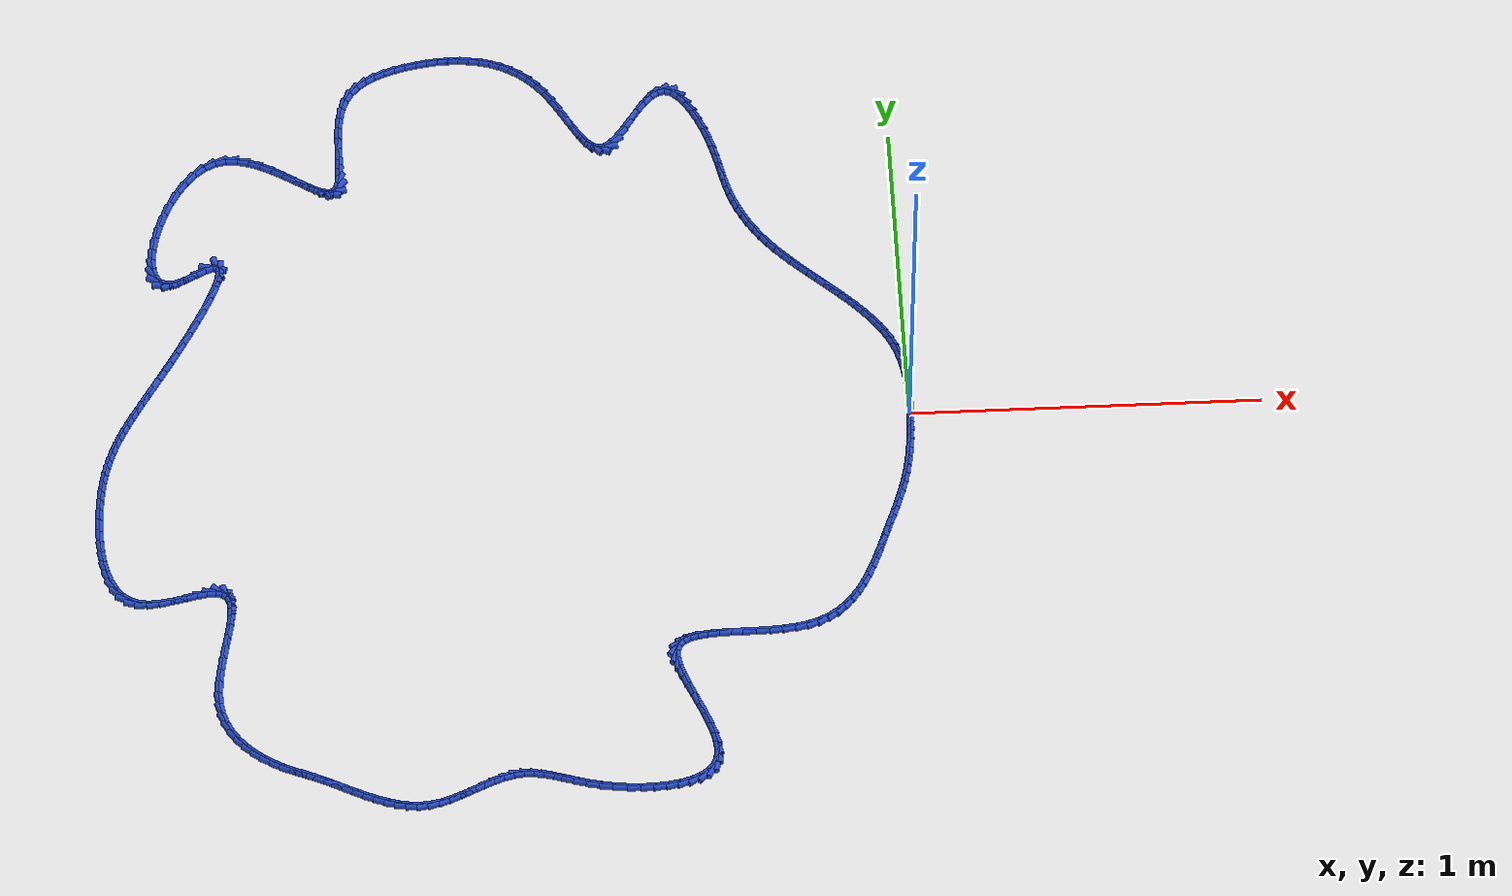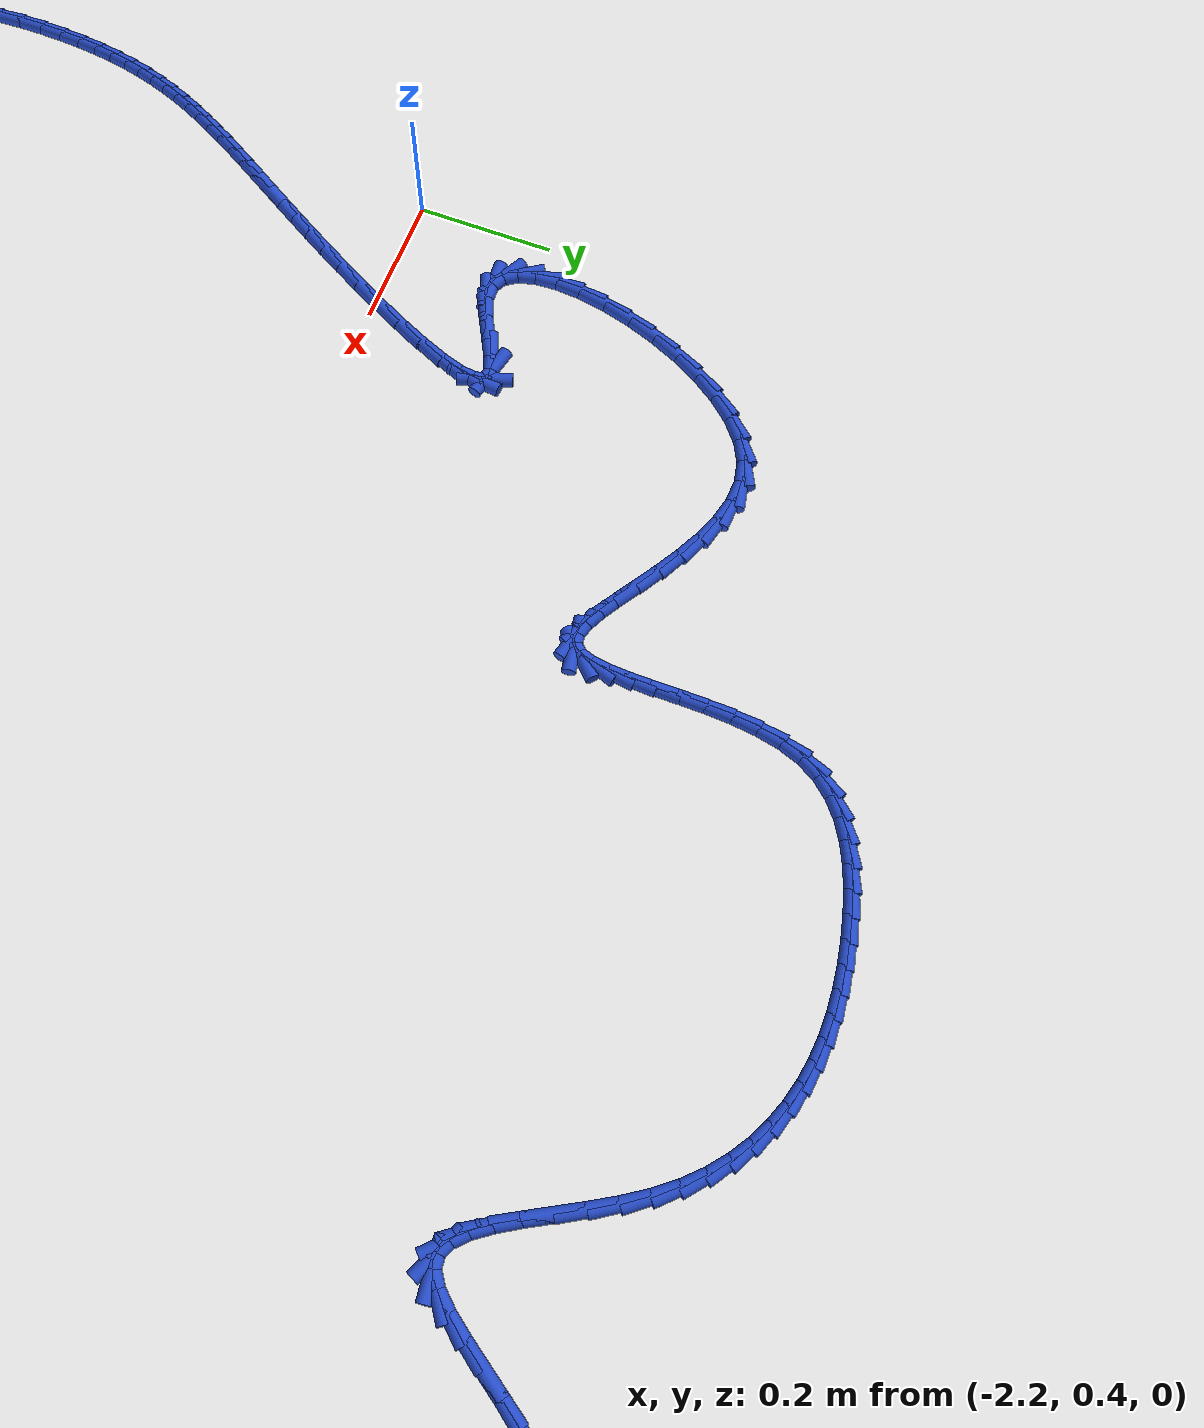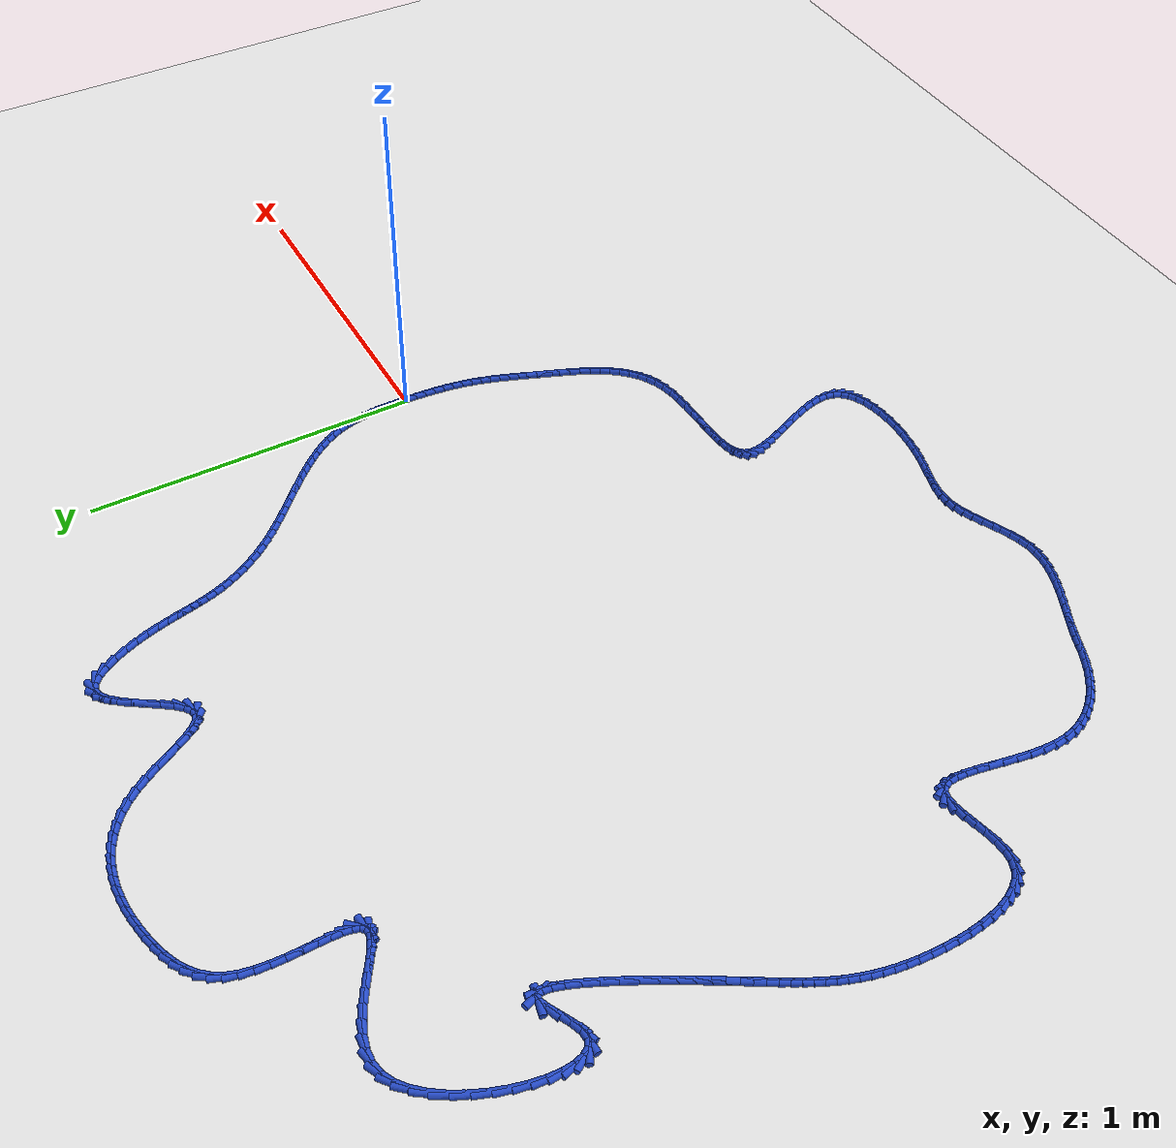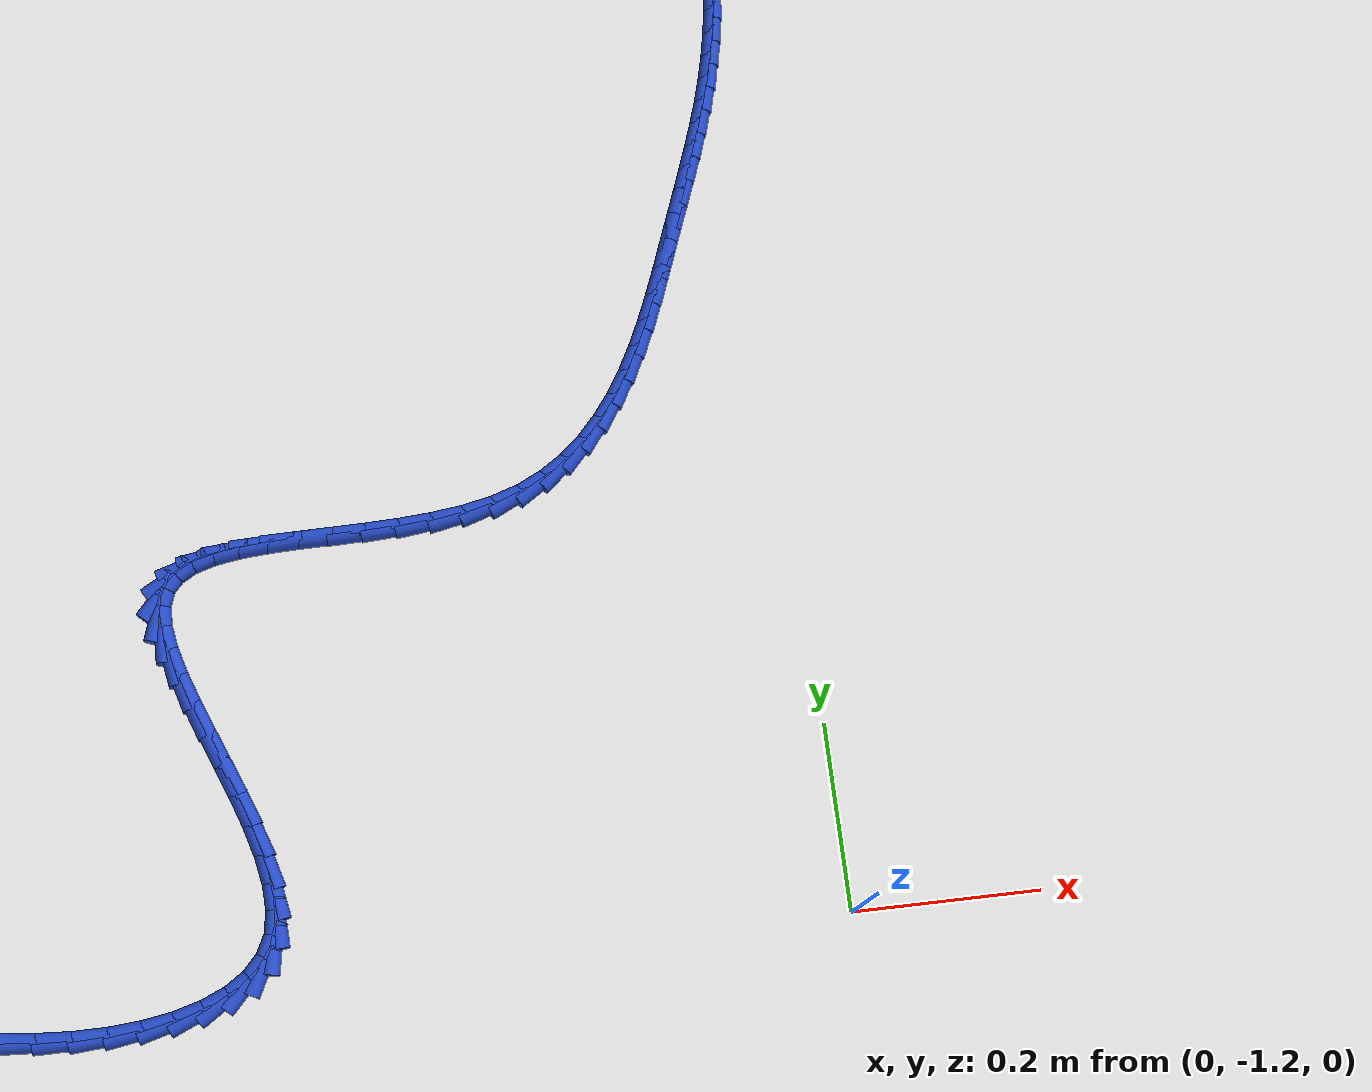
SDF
<sdf version="1.6">
 <world name="default">
  <light name="sun" type="directional">
   <pose>0 0 10 0 -0 0</pose>
   <diffuse>0.8 0.8 0.8 1</diffuse>
   <specular>0.2 0.2 0.2 1</specular>
   <attenuation>
    <range>1000</range>
    <constant>0.9</constant>
    <linear>0.01</linear>
    <quadratic>0.001</quadratic>
   </attenuation>
   <direction>-0.5 0.1 -0.9</direction>
  </light>
  <model name="ground_plane">
   <static>1</static>
   <link name="link">
    <collision name="collision">
     <geometry><plane><normal>0 0 1</normal><size>100 100</size></plane></geometry>
     <surface><friction><ode><mu>100</mu><mu2>50</mu2></ode></friction></surface>
    </collision>
    <visual name="visual">
     <cast_shadows>0</cast_shadows>
     <geometry><plane><normal>0 0 1</normal><size>100 100</size></plane></geometry>
     <material>
      <script><uri>file://media/materials/scripts/gazebo.material</uri><name>Gazebo/WhiteGlow</name></script>
     </material>
    </visual>
   </link>
  </model>
  <gravity>0 0 -9.8</gravity>
  <magnetic_field>6e-06 2.3e-05 -4.2e-05</magnetic_field>
  <atmosphere type="adiabatic"/>
  <physics name="default_physics" default="0" type="ode">
   <max_step_size>0.001</max_step_size>
   <real_time_factor>1</real_time_factor>
   <real_time_update_rate>1000</real_time_update_rate>
  </physics>
  <scene><ambient>0.4 0.4 0.4 1</ambient><background>0.7 0.7 0.7 1</background><shadows>1</shadows></scene>
  <spherical_coordinates>
   <surface_model>EARTH_WGS84</surface_model>
   <latitude_deg>0</latitude_deg>
   <longitude_deg>0</longitude_deg>
   <elevation>0</elevation>
   <heading_deg>0</heading_deg>
  </spherical_coordinates>
  <model name="line">
   <link name="link_0">
    <pose>1.6046192152785466e-17 4.163336342344337e-17 0.01 0 1.57 1.559025878039072</pose>
    <collision name="collision">
     <geometry><cylinder><radius>0.01</radius><length>0.08</length></cylinder></geometry>
    </collision>
    <visual name="visual">
     <material>
      <script><name>Gazebo/Blue</name><uri>file://media/materials/scripts/gazebo.material</uri></script>
     </material>
     <geometry><cylinder><radius>0.01</radius><length>0.08</length></cylinder></geometry>
    </visual>
   </link>
   <link name="link_1">
    <pose>0.00036611692132412993 0.031103318238790686 0.01 0 1.57 -1.558527012413176</pose>
    <collision name="collision">
     <geometry><cylinder><radius>0.01</radius><length>0.08</length></cylinder></geometry>
    </collision>
    <visual name="visual">
     <material>
      <script><name>Gazebo/Blue</name><uri>file://media/materials/scripts/gazebo.material</uri></script>
     </material>
     <geometry><cylinder><radius>0.01</radius><length>0.08</length></cylinder></geometry>
    </visual>
   </link>
   <link name="link_2">
    <pose>-1.5568919749777246e-05 0.06221073602198281 0.01 0 1.57 -1.5260380740022395</pose>
    <collision name="collision">
     <geometry><cylinder><radius>0.01</radius><length>0.08</length></cylinder></geometry>
    </collision>
    <visual name="visual">
     <material>
      <script><name>Gazebo/Blue</name><uri>file://media/materials/scripts/gazebo.material</uri></script>
     </material>
     <geometry><cylinder><radius>0.01</radius><length>0.08</length></cylinder></geometry>
    </visual>
   </link>
   <link name="link_3">
    <pose>-0.0014003664113200111 0.09312956237344915 0.01 0 1.57 -1.4844551805159991</pose>
    <collision name="collision">
     <geometry><cylinder><radius>0.01</radius><length>0.08</length></cylinder></geometry>
    </collision>
    <visual name="visual">
     <material>
      <script><name>Gazebo/Blue</name><uri>file://media/materials/scripts/gazebo.material</uri></script>
     </material>
     <geometry><cylinder><radius>0.01</radius><length>0.08</length></cylinder></geometry>
    </visual>
   </link>
   <link name="link_4">
    <pose>-0.004043584441484881 0.1236671063170625 0.01 0 1.57 -1.4329428710564218</pose>
    <collision name="collision">
     <geometry><cylinder><radius>0.01</radius><length>0.08</length></cylinder></geometry>
    </collision>
    <visual name="visual">
     <material>
      <script><name>Gazebo/Blue</name><uri>file://media/materials/scripts/gazebo.material</uri></script>
     </material>
     <geometry><cylinder><radius>0.01</radius><length>0.08</length></cylinder></geometry>
    </visual>
   </link>
   <link name="link_5">
    <pose>-0.00820053189834269 0.1536306768766956 0.01 0 1.57 -1.3705502632728215</pose>
    <collision name="collision">
     <geometry><cylinder><radius>0.01</radius><length>0.08</length></cylinder></geometry>
    </collision>
    <visual name="visual">
     <material>
      <script><name>Gazebo/Blue</name><uri>file://media/materials/scripts/gazebo.material</uri></script>
     </material>
     <geometry><cylinder><radius>0.01</radius><length>0.08</length></cylinder></geometry>
    </visual>
   </link>
   <link name="link_6">
    <pose>-0.014126517669991743 0.18282758307622118 0.01 0 1.57 -1.296349230374188</pose>
    <collision name="collision">
     <geometry><cylinder><radius>0.01</radius><length>0.08</length></cylinder></geometry>
    </collision>
    <visual name="visual">
     <material>
      <script><name>Gazebo/Blue</name><uri>file://media/materials/scripts/gazebo.material</uri></script>
     </material>
     <geometry><cylinder><radius>0.01</radius><length>0.08</length></cylinder></geometry>
    </visual>
   </link>
   <link name="link_7">
    <pose>-0.022076850644530355 0.21106513393951204 0.01 0 1.57 -1.2115966267768623</pose>
    <collision name="collision">
     <geometry><cylinder><radius>0.01</radius><length>0.08</length></cylinder></geometry>
    </collision>
    <visual name="visual">
     <material>
      <script><name>Gazebo/Blue</name><uri>file://media/materials/scripts/gazebo.material</uri></script>
     </material>
     <geometry><cylinder><radius>0.01</radius><length>0.08</length></cylinder></geometry>
    </visual>
   </link>
   <link name="link_8">
    <pose>-0.03225925524171878 0.23818281952524042 0.01 0 1.57 -1.1285021299202573</pose>
    <collision name="collision">
     <geometry><cylinder><radius>0.01</radius><length>0.08</length></cylinder></geometry>
    </collision>
    <visual name="visual">
     <material>
      <script><name>Gazebo/Blue</name><uri>file://media/materials/scripts/gazebo.material</uri></script>
     </material>
     <geometry><cylinder><radius>0.01</radius><length>0.08</length></cylinder></geometry>
    </visual>
   </link>
   <link name="link_9">
    <pose>-0.04458908963712881 0.26421785508702267 0.01 0 1.57 -1.0528841419258193</pose>
    <collision name="collision">
     <geometry><cylinder><radius>0.01</radius><length>0.08</length></cylinder></geometry>
    </collision>
    <visual name="visual">
     <material>
      <script><name>Gazebo/Blue</name><uri>file://media/materials/scripts/gazebo.material</uri></script>
     </material>
     <geometry><cylinder><radius>0.01</radius><length>0.08</length></cylinder></geometry>
    </visual>
   </link>
   <link name="link_10">
    <pose>-0.05887074644238485 0.2892825010938501 0.01 0 1.57 -0.9856624622728528</pose>
    <collision name="collision">
     <geometry><cylinder><radius>0.01</radius><length>0.08</length></cylinder></geometry>
    </collision>
    <visual name="visual">
     <material>
      <script><name>Gazebo/Blue</name><uri>file://media/materials/scripts/gazebo.material</uri></script>
     </material>
     <geometry><cylinder><radius>0.01</radius><length>0.08</length></cylinder></geometry>
    </visual>
   </link>
   <link name="link_11">
    <pose>-0.07490840553191591 0.3134891618873545 0.01 0 1.57 -0.927239807833921</pose>
    <collision name="collision">
     <geometry><cylinder><radius>0.01</radius><length>0.08</length></cylinder></geometry>
    </collision>
    <visual name="visual">
     <material>
      <script><name>Gazebo/Blue</name><uri>file://media/materials/scripts/gazebo.material</uri></script>
     </material>
     <geometry><cylinder><radius>0.01</radius><length>0.08</length></cylinder></geometry>
    </visual>
   </link>
   <link name="link_12">
    <pose>-0.09250624678015107 0.3369502418091671 0.01 0 1.57 -0.8776384261099346</pose>
    <collision name="collision">
     <geometry><cylinder><radius>0.01</radius><length>0.08</length></cylinder></geometry>
    </collision>
    <visual name="visual">
     <material>
      <script><name>Gazebo/Blue</name><uri>file://media/materials/scripts/gazebo.material</uri></script>
     </material>
     <geometry><cylinder><radius>0.01</radius><length>0.08</length></cylinder></geometry>
    </visual>
   </link>
   <link name="link_13">
    <pose>-0.11146845006151937 0.3597781452009199 0.01 0 1.57 -0.8366373205063286</pose>
    <collision name="collision">
     <geometry><cylinder><radius>0.01</radius><length>0.08</length></cylinder></geometry>
    </collision>
    <visual name="visual">
     <material>
      <script><name>Gazebo/Blue</name><uri>file://media/materials/scripts/gazebo.material</uri></script>
     </material>
     <geometry><cylinder><radius>0.01</radius><length>0.08</length></cylinder></geometry>
    </visual>
   </link>
   <link name="link_14">
    <pose>-0.13159919525044989 0.3820852764042439 0.01 0 1.57 -0.8038903607541457</pose>
    <collision name="collision">
     <geometry><cylinder><radius>0.01</radius><length>0.08</length></cylinder></geometry>
    </collision>
    <visual name="visual">
     <material>
      <script><name>Gazebo/Blue</name><uri>file://media/materials/scripts/gazebo.material</uri></script>
     </material>
     <geometry><cylinder><radius>0.01</radius><length>0.08</length></cylinder></geometry>
    </visual>
   </link>
   <link name="link_15">
    <pose>-0.15270266222137163 0.4039840397607711 0.01 0 1.57 -0.7790148887713376</pose>
    <collision name="collision">
     <geometry><cylinder><radius>0.01</radius><length>0.08</length></cylinder></geometry>
    </collision>
    <visual name="visual">
     <material>
      <script><name>Gazebo/Blue</name><uri>file://media/materials/scripts/gazebo.material</uri></script>
     </material>
     <geometry><cylinder><radius>0.01</radius><length>0.08</length></cylinder></geometry>
    </visual>
   </link>
   <link name="link_16">
    <pose>-0.17458303084871368 0.42558683961213273 0.01 0 1.57 -0.761651646574452</pose>
    <collision name="collision">
     <geometry><cylinder><radius>0.01</radius><length>0.08</length></cylinder></geometry>
    </collision>
    <visual name="visual">
     <material>
      <script><name>Gazebo/Blue</name><uri>file://media/materials/scripts/gazebo.material</uri></script>
     </material>
     <geometry><cylinder><radius>0.01</radius><length>0.08</length></cylinder></geometry>
    </visual>
   </link>
   <link name="link_17">
    <pose>-0.19704448100690494 0.44700608029996025 0.01 0 1.57 -0.7515016013901794</pose>
    <collision name="collision">
     <geometry><cylinder><radius>0.01</radius><length>0.08</length></cylinder></geometry>
    </collision>
    <visual name="visual">
     <material>
      <script><name>Gazebo/Blue</name><uri>file://media/materials/scripts/gazebo.material</uri></script>
     </material>
     <geometry><cylinder><radius>0.01</radius><length>0.08</length></cylinder></geometry>
    </visual>
   </link>
   <link name="link_18">
    <pose>-0.21989119257037476 0.46835416616588577 0.01 0 1.57 -0.7483459253022219</pose>
    <collision name="collision">
     <geometry><cylinder><radius>0.01</radius><length>0.08</length></cylinder></geometry>
    </collision>
    <visual name="visual">
     <material>
      <script><name>Gazebo/Blue</name><uri>file://media/materials/scripts/gazebo.material</uri></script>
     </material>
     <geometry><cylinder><radius>0.01</radius><length>0.08</length></cylinder></geometry>
    </visual>
   </link>
   <link name="link_19">
    <pose>-0.24292734541355188 0.4897435015515403 0.01 0 1.57 -0.7520541750924424</pose>
    <collision name="collision">
     <geometry><cylinder><radius>0.01</radius><length>0.08</length></cylinder></geometry>
    </collision>
    <visual name="visual">
     <material>
      <script><name>Gazebo/Blue</name><uri>file://media/materials/scripts/gazebo.material</uri></script>
     </material>
     <geometry><cylinder><radius>0.01</radius><length>0.08</length></cylinder></geometry>
    </visual>
   </link>
   <link name="link_20">
    <pose>-0.26595711941086553 0.5112864907985555 0.01 0 1.57 -0.7625839180046503</pose>
    <collision name="collision">
     <geometry><cylinder><radius>0.01</radius><length>0.08</length></cylinder></geometry>
    </collision>
    <visual name="visual">
     <material>
      <script><name>Gazebo/Blue</name><uri>file://media/materials/scripts/gazebo.material</uri></script>
     </material>
     <geometry><cylinder><radius>0.01</radius><length>0.08</length></cylinder></geometry>
    </visual>
   </link>
   <link name="link_21">
    <pose>-0.2887846944367449 0.5330955382485633 0.01 0 1.57 -0.7799732535611396</pose>
    <collision name="collision">
     <geometry><cylinder><radius>0.01</radius><length>0.08</length></cylinder></geometry>
    </collision>
    <visual name="visual">
     <material>
      <script><name>Gazebo/Blue</name><uri>file://media/materials/scripts/gazebo.material</uri></script>
     </material>
     <geometry><cylinder><radius>0.01</radius><length>0.08</length></cylinder></geometry>
    </visual>
   </link>
   <link name="link_22">
    <pose>-0.3112142503656186 0.5552830482431945 0.01 0 1.57 -0.8043260909817267</pose>
    <collision name="collision">
     <geometry><cylinder><radius>0.01</radius><length>0.08</length></cylinder></geometry>
    </collision>
    <visual name="visual">
     <material>
      <script><name>Gazebo/Blue</name><uri>file://media/materials/scripts/gazebo.material</uri></script>
     </material>
     <geometry><cylinder><radius>0.01</radius><length>0.08</length></cylinder></geometry>
    </visual>
   </link>
   <link name="link_23">
    <pose>-0.333049967071916 0.5779614251240812 0.01 0 1.57 -0.8357887305561135</pose>
    <collision name="collision">
     <geometry><cylinder><radius>0.01</radius><length>0.08</length></cylinder></geometry>
    </collision>
    <visual name="visual">
     <material>
      <script><name>Gazebo/Blue</name><uri>file://media/materials/scripts/gazebo.material</uri></script>
     </material>
     <geometry><cylinder><radius>0.01</radius><length>0.08</length></cylinder></geometry>
    </visual>
   </link>
   <link name="link_24">
    <pose>-0.35409602443006627 0.601243073232855 0.01 0 1.57 -0.8745154024992673</pose>
    <collision name="collision">
     <geometry><cylinder><radius>0.01</radius><length>0.08</length></cylinder></geometry>
    </collision>
    <visual name="visual">
     <material>
      <script><name>Gazebo/Blue</name><uri>file://media/materials/scripts/gazebo.material</uri></script>
     </material>
     <geometry><cylinder><radius>0.01</radius><length>0.08</length></cylinder></geometry>
    </visual>
   </link>
   <link name="link_25">
    <pose>-0.37415660231449815 0.6252403969111471 0.01 0 1.57 -0.9206202751416523</pose>
    <collision name="collision">
     <geometry><cylinder><radius>0.01</radius><length>0.08</length></cylinder></geometry>
    </collision>
    <visual name="visual">
     <material>
      <script><name>Gazebo/Blue</name><uri>file://media/materials/scripts/gazebo.material</uri></script>
     </material>
     <geometry><cylinder><radius>0.01</radius><length>0.08</length></cylinder></geometry>
    </visual>
   </link>
   <link name="link_26">
    <pose>-0.3930358805996407 0.6500658005005888 0.01 0 1.57 -0.9731091699910684</pose>
    <collision name="collision">
     <geometry><cylinder><radius>0.01</radius><length>0.08</length></cylinder></geometry>
    </collision>
    <visual name="visual">
     <material>
      <script><name>Gazebo/Blue</name><uri>file://media/materials/scripts/gazebo.material</uri></script>
     </material>
     <geometry><cylinder><radius>0.01</radius><length>0.08</length></cylinder></geometry>
    </visual>
   </link>
   <link name="link_27">
    <pose>-0.410550807948935 0.6757947896407362 0.01 0 1.57 -1.0262132315540728</pose>
    <collision name="collision">
     <geometry><cylinder><radius>0.01</radius><length>0.08</length></cylinder></geometry>
    </collision>
    <visual name="visual">
     <material>
      <script><name>Gazebo/Blue</name><uri>file://media/materials/scripts/gazebo.material</uri></script>
     </material>
     <geometry><cylinder><radius>0.01</radius><length>0.08</length></cylinder></geometry>
    </visual>
   </link>
   <link name="link_28">
    <pose>-0.42659430295802186 0.7022833353001264 0.01 0 1.57 -1.0785201466216954</pose>
    <collision name="collision">
     <geometry><cylinder><radius>0.01</radius><length>0.08</length></cylinder></geometry>
    </collision>
    <visual name="visual">
     <material>
      <script><name>Gazebo/Blue</name><uri>file://media/materials/scripts/gazebo.material</uri></script>
     </material>
     <geometry><cylinder><radius>0.01</radius><length>0.08</length></cylinder></geometry>
    </visual>
   </link>
   <link name="link_29">
    <pose>-0.4410872674943606 0.7293065435814905 0.01 0 1.57 -1.1309279285800542</pose>
    <collision name="collision">
     <geometry><cylinder><radius>0.01</radius><length>0.08</length></cylinder></geometry>
    </collision>
    <visual name="visual">
     <material>
      <script><name>Gazebo/Blue</name><uri>file://media/materials/scripts/gazebo.material</uri></script>
     </material>
     <geometry><cylinder><radius>0.01</radius><length>0.08</length></cylinder></geometry>
    </visual>
   </link>
   <link name="link_30">
    <pose>-0.4539506472248995 0.7566393940176628 0.01 0 1.57 -1.1844005741677366</pose>
    <collision name="collision">
     <geometry><cylinder><radius>0.01</radius><length>0.08</length></cylinder></geometry>
    </collision>
    <visual name="visual">
     <material>
      <script><name>Gazebo/Blue</name><uri>file://media/materials/scripts/gazebo.material</uri></script>
     </material>
     <geometry><cylinder><radius>0.01</radius><length>0.08</length></cylinder></geometry>
    </visual>
   </link>
   <link name="link_31">
    <pose>-0.4651053878165873 0.7840568661414786 0.01 0 1.57 -1.239612823315265</pose>
    <collision name="collision">
     <geometry><cylinder><radius>0.01</radius><length>0.08</length></cylinder></geometry>
    </collision>
    <visual name="visual">
     <material>
      <script><name>Gazebo/Blue</name><uri>file://media/materials/scripts/gazebo.material</uri></script>
     </material>
     <geometry><cylinder><radius>0.01</radius><length>0.08</length></cylinder></geometry>
    </visual>
   </link>
   <link name="link_32">
    <pose>-0.4744890626398107 0.8113470680955398 0.01 0 1.57 -1.289584873853484</pose>
    <collision name="collision">
     <geometry><cylinder><radius>0.01</radius><length>0.08</length></cylinder></geometry>
    </collision>
    <visual name="visual">
     <material>
      <script><name>Gazebo/Blue</name><uri>file://media/materials/scripts/gazebo.material</uri></script>
     </material>
     <geometry><cylinder><radius>0.01</radius><length>0.08</length></cylinder></geometry>
    </visual>
   </link>
   <link name="link_33">
    <pose>-0.4823437676717832 0.8385385476288543 0.01 0 1.57 -1.32576523492219</pose>
    <collision name="collision">
     <geometry><cylinder><radius>0.01</radius><length>0.08</length></cylinder></geometry>
    </collision>
    <visual name="visual">
     <material>
      <script><name>Gazebo/Blue</name><uri>file://media/materials/scripts/gazebo.material</uri></script>
     </material>
     <geometry><cylinder><radius>0.01</radius><length>0.08</length></cylinder></geometry>
    </visual>
   </link>
   <link name="link_34">
    <pose>-0.48917825107933516 0.8658703910385768 0.01 0 1.57 -1.346209093152567</pose>
    <collision name="collision">
     <geometry><cylinder><radius>0.01</radius><length>0.08</length></cylinder></geometry>
    </collision>
    <visual name="visual">
     <material>
      <script><name>Gazebo/Blue</name><uri>file://media/materials/scripts/gazebo.material</uri></script>
     </material>
     <geometry><cylinder><radius>0.01</radius><length>0.08</length></cylinder></geometry>
    </visual>
   </link>
   <link name="link_35">
    <pose>-0.49551027275156 0.8935887999391006 0.01 0 1.57 -1.350546205599193</pose>
    <collision name="collision">
     <geometry><cylinder><radius>0.01</radius><length>0.08</length></cylinder></geometry>
    </collision>
    <visual name="visual">
     <material>
      <script><name>Gazebo/Blue</name><uri>file://media/materials/scripts/gazebo.material</uri></script>
     </material>
     <geometry><cylinder><radius>0.01</radius><length>0.08</length></cylinder></geometry>
    </visual>
   </link>
   <link name="link_36">
    <pose>-0.5018575925775507 0.9219399759448187 0.01 0 1.57 -1.3396182417893663</pose>
    <collision name="collision">
     <geometry><cylinder><radius>0.01</radius><length>0.08</length></cylinder></geometry>
    </collision>
    <visual name="visual">
     <material>
      <script><name>Gazebo/Blue</name><uri>file://media/materials/scripts/gazebo.material</uri></script>
     </material>
     <geometry><cylinder><radius>0.01</radius><length>0.08</length></cylinder></geometry>
    </visual>
   </link>
   <link name="link_37">
    <pose>-0.5087379704464009 0.9511701206701247 0.01 0 1.57 -1.3152309533505668</pose>
    <collision name="collision">
     <geometry><cylinder><radius>0.01</radius><length>0.08</length></cylinder></geometry>
    </collision>
    <visual name="visual">
     <material>
      <script><name>Gazebo/Blue</name><uri>file://media/materials/scripts/gazebo.material</uri></script>
     </material>
     <geometry><cylinder><radius>0.01</radius><length>0.08</length></cylinder></geometry>
    </visual>
   </link>
   <link name="link_38">
    <pose>-0.5166691662472036 0.9815254357294112 0.01 0 1.57 -1.2798668388969523</pose>
    <collision name="collision">
     <geometry><cylinder><radius>0.01</radius><length>0.08</length></cylinder></geometry>
    </collision>
    <visual name="visual">
     <material>
      <script><name>Gazebo/Blue</name><uri>file://media/materials/scripts/gazebo.material</uri></script>
     </material>
     <geometry><cylinder><radius>0.01</radius><length>0.08</length></cylinder></geometry>
    </visual>
   </link>
   <link name="link_39">
    <pose>-0.5261689398690522 1.0132521227370723 0.01 0 1.57 -1.23637765767313</pose>
    <collision name="collision">
     <geometry><cylinder><radius>0.01</radius><length>0.08</length></cylinder></geometry>
    </collision>
    <visual name="visual">
     <material>
      <script><name>Gazebo/Blue</name><uri>file://media/materials/scripts/gazebo.material</uri></script>
     </material>
     <geometry><cylinder><radius>0.01</radius><length>0.08</length></cylinder></geometry>
    </visual>
   </link>
   <link name="link_40">
    <pose>-0.5377549773394633 1.0465961676912587 0.01 0 1.57 -1.186841311415604</pose>
    <collision name="collision">
     <geometry><cylinder><radius>0.01</radius><length>0.08</length></cylinder></geometry>
    </collision>
    <visual name="visual">
     <material>
      <script><name>Gazebo/Blue</name><uri>file://media/materials/scripts/gazebo.material</uri></script>
     </material>
     <geometry><cylinder><radius>0.01</radius><length>0.08</length></cylinder></geometry>
    </visual>
   </link>
   <link name="link_41">
    <pose>-0.5517553712232236 1.0812500965676453 0.01 0 1.57 -1.1264358655861058</pose>
    <collision name="collision">
     <geometry><cylinder><radius>0.01</radius><length>0.08</length></cylinder></geometry>
    </collision>
    <visual name="visual">
     <material>
      <script><name>Gazebo/Blue</name><uri>file://media/materials/scripts/gazebo.material</uri></script>
     </material>
     <geometry><cylinder><radius>0.01</radius><length>0.08</length></cylinder></geometry>
    </visual>
   </link>
   <link name="link_42">
    <pose>-0.5678985544465788 1.1151559127645638 0.01 0 1.57 -1.0437890577623303</pose>
    <collision name="collision">
     <geometry><cylinder><radius>0.01</radius><length>0.08</length></cylinder></geometry>
    </collision>
    <visual name="visual">
     <material>
      <script><name>Gazebo/Blue</name><uri>file://media/materials/scripts/gazebo.material</uri></script>
     </material>
     <geometry><cylinder><radius>0.01</radius><length>0.08</length></cylinder></geometry>
    </visual>
   </link>
   <link name="link_43">
    <pose>-0.5857946880035982 1.1459103610132044 0.01 0 1.57 -0.9182304434406863</pose>
    <collision name="collision">
     <geometry><cylinder><radius>0.01</radius><length>0.08</length></cylinder></geometry>
    </collision>
    <visual name="visual">
     <material>
      <script><name>Gazebo/Blue</name><uri>file://media/materials/scripts/gazebo.material</uri></script>
     </material>
     <geometry><cylinder><radius>0.01</radius><length>0.08</length></cylinder></geometry>
    </visual>
   </link>
   <link name="link_44">
    <pose>-0.6050539328883511 1.171110186044757 0.01 0 1.57 -0.7057640332321349</pose>
    <collision name="collision">
     <geometry><cylinder><radius>0.01</radius><length>0.08</length></cylinder></geometry>
    </collision>
    <visual name="visual">
     <material>
      <script><name>Gazebo/Blue</name><uri>file://media/materials/scripts/gazebo.material</uri></script>
     </material>
     <geometry><cylinder><radius>0.01</radius><length>0.08</length></cylinder></geometry>
    </visual>
   </link>
   <link name="link_45">
    <pose>-0.6252864500949067 1.1883521325904123 0.01 0 1.57 -0.3192478120041244</pose>
    <collision name="collision">
     <geometry><cylinder><radius>0.01</radius><length>0.08</length></cylinder></geometry>
    </collision>
    <visual name="visual">
     <material>
      <script><name>Gazebo/Blue</name><uri>file://media/materials/scripts/gazebo.material</uri></script>
     </material>
     <geometry><cylinder><radius>0.01</radius><length>0.08</length></cylinder></geometry>
    </visual>
   </link>
   <link name="link_46">
    <pose>-0.6461024006173343 1.1952329453813604 0.01 0 1.57 0.24886269692223045</pose>
    <collision name="collision">
     <geometry><cylinder><radius>0.01</radius><length>0.08</length></cylinder></geometry>
    </collision>
    <visual name="visual">
     <material>
      <script><name>Gazebo/Blue</name><uri>file://media/materials/scripts/gazebo.material</uri></script>
     </material>
     <geometry><cylinder><radius>0.01</radius><length>0.08</length></cylinder></geometry>
    </visual>
   </link>
   <link name="link_47">
    <pose>-0.6671425145218755 1.1898860040294852 0.01 0 1.57 0.6513745547622711</pose>
    <collision name="collision">
     <geometry><cylinder><radius>0.01</radius><length>0.08</length></cylinder></geometry>
    </collision>
    <visual name="visual">
     <material>
      <script><name>Gazebo/Blue</name><uri>file://media/materials/scripts/gazebo.material</uri></script>
     </material>
     <geometry><cylinder><radius>0.01</radius><length>0.08</length></cylinder></geometry>
    </visual>
   </link>
   <link name="link_48">
    <pose>-0.6882388091522095 1.1738027038798802 0.01 0 1.57 0.8512526315606326</pose>
    <collision name="collision">
     <geometry><cylinder><radius>0.01</radius><length>0.08</length></cylinder></geometry>
    </collision>
    <visual name="visual">
     <material>
      <script><name>Gazebo/Blue</name><uri>file://media/materials/scripts/gazebo.material</uri></script>
     </material>
     <geometry><cylinder><radius>0.01</radius><length>0.08</length></cylinder></geometry>
    </visual>
   </link>
   <link name="link_49">
    <pose>-0.7092971407823271 1.1497706701839614 0.01 0 1.57 0.9488223527337029</pose>
    <collision name="collision">
     <geometry><cylinder><radius>0.01</radius><length>0.08</length></cylinder></geometry>
    </collision>
    <visual name="visual">
     <material>
      <script><name>Gazebo/Blue</name><uri>file://media/materials/scripts/gazebo.material</uri></script>
     </material>
     <geometry><cylinder><radius>0.01</radius><length>0.08</length></cylinder></geometry>
    </visual>
   </link>
   <link name="link_50">
    <pose>-0.7302235233432267 1.1205802958351792 0.01 0 1.57 0.9902548783657289</pose>
    <collision name="collision">
     <geometry><cylinder><radius>0.01</radius><length>0.08</length></cylinder></geometry>
    </collision>
    <visual name="visual">
     <material>
      <script><name>Gazebo/Blue</name><uri>file://media/materials/scripts/gazebo.material</uri></script>
     </material>
     <geometry><cylinder><radius>0.01</radius><length>0.08</length></cylinder></geometry>
    </visual>
   </link>
   <link name="link_51">
    <pose>-0.7509239707659062 1.0890219737269826 0.01 0 1.57 0.9912170642530256</pose>
    <collision name="collision">
     <geometry><cylinder><radius>0.01</radius><length>0.08</length></cylinder></geometry>
    </collision>
    <visual name="visual">
     <material>
      <script><name>Gazebo/Blue</name><uri>file://media/materials/scripts/gazebo.material</uri></script>
     </material>
     <geometry><cylinder><radius>0.01</radius><length>0.08</length></cylinder></geometry>
    </visual>
   </link>
   <link name="link_52">
    <pose>-0.7713044969813639 1.0578860967528207 0.01 0 1.57 0.9500350199147481</pose>
    <collision name="collision">
     <geometry><cylinder><radius>0.01</radius><length>0.08</length></cylinder></geometry>
    </collision>
    <visual name="visual">
     <material>
      <script><name>Gazebo/Blue</name><uri>file://media/materials/scripts/gazebo.material</uri></script>
     </material>
     <geometry><cylinder><radius>0.01</radius><length>0.08</length></cylinder></geometry>
    </visual>
   </link>
   <link name="link_53">
    <pose>-0.7912711159205982 1.029963057806144 0.01 0 1.57 0.8448054525535259</pose>
    <collision name="collision">
     <geometry><cylinder><radius>0.01</radius><length>0.08</length></cylinder></geometry>
    </collision>
    <visual name="visual">
     <material>
      <script><name>Gazebo/Blue</name><uri>file://media/materials/scripts/gazebo.material</uri></script>
     </material>
     <geometry><cylinder><radius>0.01</radius><length>0.08</length></cylinder></geometry>
    </visual>
   </link>
   <link name="link_54">
    <pose>-0.8107298415146063 1.008043249780401 0.01 0 1.57 0.6081013437501183</pose>
    <collision name="collision">
     <geometry><cylinder><radius>0.01</radius><length>0.08</length></cylinder></geometry>
    </collision>
    <visual name="visual">
     <material>
      <script><name>Gazebo/Blue</name><uri>file://media/materials/scripts/gazebo.material</uri></script>
     </material>
     <geometry><cylinder><radius>0.01</radius><length>0.08</length></cylinder></geometry>
    </visual>
   </link>
   <link name="link_55">
    <pose>-0.8295866876943869 0.9949170655690416 0.01 0 1.57 0.11258326718776103</pose>
    <collision name="collision">
     <geometry><cylinder><radius>0.01</radius><length>0.08</length></cylinder></geometry>
    </collision>
    <visual name="visual">
     <material>
      <script><name>Gazebo/Blue</name><uri>file://media/materials/scripts/gazebo.material</uri></script>
     </material>
     <geometry><cylinder><radius>0.01</radius><length>0.08</length></cylinder></geometry>
    </visual>
   </link>
   <link name="link_56">
    <pose>-0.8477871687073082 0.9928592945196167 0.01 0 1.57 -0.43918239282443244</pose>
    <collision name="collision">
     <geometry><cylinder><radius>0.01</radius><length>0.08</length></cylinder></geometry>
    </collision>
    <visual name="visual">
     <material>
      <script><name>Gazebo/Blue</name><uri>file://media/materials/scripts/gazebo.material</uri></script>
     </material>
     <geometry><cylinder><radius>0.01</radius><length>0.08</length></cylinder></geometry>
    </visual>
   </link>
   <link name="link_57">
    <pose>-0.8655037552354329 1.0011822296442745 0.01 0 1.57 -0.7701243020527541</pose>
    <collision name="collision">
     <geometry><cylinder><radius>0.01</radius><length>0.08</length></cylinder></geometry>
    </collision>
    <visual name="visual">
     <material>
      <script><name>Gazebo/Blue</name><uri>file://media/materials/scripts/gazebo.material</uri></script>
     </material>
     <geometry><cylinder><radius>0.01</radius><length>0.08</length></cylinder></geometry>
    </visual>
   </link>
   <link name="link_58">
    <pose>-0.8829898204943766 1.0181421310671979 0.01 0 1.57 -0.9375657963978437</pose>
    <collision name="collision">
     <geometry><cylinder><radius>0.01</radius><length>0.08</length></cylinder></geometry>
    </collision>
    <visual name="visual">
     <material>
      <script><name>Gazebo/Blue</name><uri>file://media/materials/scripts/gazebo.material</uri></script>
     </material>
     <geometry><cylinder><radius>0.01</radius><length>0.08</length></cylinder></geometry>
    </visual>
   </link>
   <link name="link_59">
    <pose>-0.9004988370922988 1.0419939615268026 0.01 0 1.57 -1.020641632821619</pose>
    <collision name="collision">
     <geometry><cylinder><radius>0.01</radius><length>0.08</length></cylinder></geometry>
    </collision>
    <visual name="visual">
     <material>
      <script><name>Gazebo/Blue</name><uri>file://media/materials/scripts/gazebo.material</uri></script>
     </material>
     <geometry><cylinder><radius>0.01</radius><length>0.08</length></cylinder></geometry>
    </visual>
   </link>
   <link name="link_60">
    <pose>-0.9182842776373588 1.0709926837615042 0.01 0 1.57 -1.0562989901425432</pose>
    <collision name="collision">
     <geometry><cylinder><radius>0.01</radius><length>0.08</length></cylinder></geometry>
    </collision>
    <visual name="visual">
     <material>
      <script><name>Gazebo/Blue</name><uri>file://media/materials/scripts/gazebo.material</uri></script>
     </material>
     <geometry><cylinder><radius>0.01</radius><length>0.08</length></cylinder></geometry>
    </visual>
   </link>
   <link name="link_61">
    <pose>-0.9365996147377165 1.1033932605097192 0.01 0 1.57 -1.0597143951358174</pose>
    <collision name="collision">
     <geometry><cylinder><radius>0.01</radius><length>0.08</length></cylinder></geometry>
    </collision>
    <visual name="visual">
     <material>
      <script><name>Gazebo/Blue</name><uri>file://media/materials/scripts/gazebo.material</uri></script>
     </material>
     <geometry><cylinder><radius>0.01</radius><length>0.08</length></cylinder></geometry>
    </visual>
   </link>
   <link name="link_62">
    <pose>-0.9556983210015311 1.1374506545098626 0.01 0 1.57 -1.0357177892746015</pose>
    <collision name="collision">
     <geometry><cylinder><radius>0.01</radius><length>0.08</length></cylinder></geometry>
    </collision>
    <visual name="visual">
     <material>
      <script><name>Gazebo/Blue</name><uri>file://media/materials/scripts/gazebo.material</uri></script>
     </material>
     <geometry><cylinder><radius>0.01</radius><length>0.08</length></cylinder></geometry>
    </visual>
   </link>
   <link name="link_63">
    <pose>-0.9758338690369625 1.1714198285003508 0.01 0 1.57 -0.9827524060793504</pose>
    <collision name="collision">
     <geometry><cylinder><radius>0.01</radius><length>0.08</length></cylinder></geometry>
    </collision>
    <visual name="visual">
     <material>
      <script><name>Gazebo/Blue</name><uri>file://media/materials/scripts/gazebo.material</uri></script>
     </material>
     <geometry><cylinder><radius>0.01</radius><length>0.08</length></cylinder></geometry>
    </visual>
   </link>
   <link name="link_64">
    <pose>-0.9972597314521701 1.2035557452196002 0.01 0 1.57 -0.8961247400660588</pose>
    <collision name="collision">
     <geometry><cylinder><radius>0.01</radius><length>0.08</length></cylinder></geometry>
    </collision>
    <visual name="visual">
     <material>
      <script><name>Gazebo/Blue</name><uri>file://media/materials/scripts/gazebo.material</uri></script>
     </material>
     <geometry><cylinder><radius>0.01</radius><length>0.08</length></cylinder></geometry>
    </visual>
   </link>
   <link name="link_65">
    <pose>-1.020203664239343 1.232239739232126 0.01 0 1.57 -0.7920952872445507</pose>
    <collision name="collision">
     <geometry><cylinder><radius>0.01</radius><length>0.08</length></cylinder></geometry>
    </collision>
    <visual name="visual">
     <material>
      <script><name>Gazebo/Blue</name><uri>file://media/materials/scripts/gazebo.material</uri></script>
     </material>
     <geometry><cylinder><radius>0.01</radius><length>0.08</length></cylinder></geometry>
    </visual>
   </link>
   <link name="link_66">
    <pose>-1.0446556690468858 1.2570214734167857 0.01 0 1.57 -0.6842038319890776</pose>
    <collision name="collision">
     <geometry><cylinder><radius>0.01</radius><length>0.08</length></cylinder></geometry>
    </collision>
    <visual name="visual">
     <material>
      <script><name>Gazebo/Blue</name><uri>file://media/materials/scripts/gazebo.material</uri></script>
     </material>
     <geometry><cylinder><radius>0.01</radius><length>0.08</length></cylinder></geometry>
    </visual>
   </link>
   <link name="link_67">
    <pose>-1.0704771650979097 1.27808246656643 0.01 0 1.57 -0.5749373845861934</pose>
    <collision name="collision">
     <geometry><cylinder><radius>0.01</radius><length>0.08</length></cylinder></geometry>
    </collision>
    <visual name="visual">
     <material>
      <script><name>Gazebo/Blue</name><uri>file://media/materials/scripts/gazebo.material</uri></script>
     </material>
     <geometry><cylinder><radius>0.01</radius><length>0.08</length></cylinder></geometry>
    </visual>
   </link>
   <link name="link_68">
    <pose>-1.097528310537443 1.2956104344300075 0.01 0 1.57 -0.46683166220466393</pose>
    <collision name="collision">
     <geometry><cylinder><radius>0.01</radius><length>0.08</length></cylinder></geometry>
    </collision>
    <visual name="visual">
     <material>
      <script><name>Gazebo/Blue</name><uri>file://media/materials/scripts/gazebo.material</uri></script>
     </material>
     <geometry><cylinder><radius>0.01</radius><length>0.08</length></cylinder></geometry>
    </visual>
   </link>
   <link name="link_69">
    <pose>-1.125669263510513 1.3097930927564652 0.01 0 1.57 -0.36226106796924157</pose>
    <collision name="collision">
     <geometry><cylinder><radius>0.01</radius><length>0.08</length></cylinder></geometry>
    </collision>
    <visual name="visual">
     <material>
      <script><name>Gazebo/Blue</name><uri>file://media/materials/scripts/gazebo.material</uri></script>
     </material>
     <geometry><cylinder><radius>0.01</radius><length>0.08</length></cylinder></geometry>
    </visual>
   </link>
   <link name="link_70">
    <pose>-1.1547601821621483 1.3208181572947517 0.01 0 1.57 -0.2631477055316021</pose>
    <collision name="collision">
     <geometry><cylinder><radius>0.01</radius><length>0.08</length></cylinder></geometry>
    </collision>
    <visual name="visual">
     <material>
      <script><name>Gazebo/Blue</name><uri>file://media/materials/scripts/gazebo.material</uri></script>
     </material>
     <geometry><cylinder><radius>0.01</radius><length>0.08</length></cylinder></geometry>
    </visual>
   </link>
   <link name="link_71">
    <pose>-1.1846612246373776 1.3288733437938154 0.01 0 1.57 -0.17080211649465463</pose>
    <collision name="collision">
     <geometry><cylinder><radius>0.01</radius><length>0.08</length></cylinder></geometry>
    </collision>
    <visual name="visual">
     <material>
      <script><name>Gazebo/Blue</name><uri>file://media/materials/scripts/gazebo.material</uri></script>
     </material>
     <geometry><cylinder><radius>0.01</radius><length>0.08</length></cylinder></geometry>
    </visual>
   </link>
   <link name="link_72">
    <pose>-1.2152325490812286 1.3341463680026033 0.01 0 1.57 -0.08591102565120334</pose>
    <collision name="collision">
     <geometry><cylinder><radius>0.01</radius><length>0.08</length></cylinder></geometry>
    </collision>
    <visual name="visual">
     <material>
      <script><name>Gazebo/Blue</name><uri>file://media/materials/scripts/gazebo.material</uri></script>
     </material>
     <geometry><cylinder><radius>0.01</radius><length>0.08</length></cylinder></geometry>
    </visual>
   </link>
   <link name="link_73">
    <pose>-1.2463343136387295 1.3368249456700645 0.01 0 1.57 -0.008631937998209965</pose>
    <collision name="collision">
     <geometry><cylinder><radius>0.01</radius><length>0.08</length></cylinder></geometry>
    </collision>
    <visual name="visual">
     <material>
      <script><name>Gazebo/Blue</name><uri>file://media/materials/scripts/gazebo.material</uri></script>
     </material>
     <geometry><cylinder><radius>0.01</radius><length>0.08</length></cylinder></geometry>
    </visual>
   </link>
   <link name="link_74">
    <pose>-1.2778266764549087 1.3370967925451467 0.01 0 1.57 0.06126466038014957</pose>
    <collision name="collision">
     <geometry><cylinder><radius>0.01</radius><length>0.08</length></cylinder></geometry>
    </collision>
    <visual name="visual">
     <material>
      <script><name>Gazebo/Blue</name><uri>file://media/materials/scripts/gazebo.material</uri></script>
     </material>
     <geometry><cylinder><radius>0.01</radius><length>0.08</length></cylinder></geometry>
    </visual>
   </link>
   <link name="link_75">
    <pose>-1.3095697956747943 1.3351496243767977 0.01 0 1.57 0.1242533988165497</pose>
    <collision name="collision">
     <geometry><cylinder><radius>0.01</radius><length>0.08</length></cylinder></geometry>
    </collision>
    <visual name="visual">
     <material>
      <script><name>Gazebo/Blue</name><uri>file://media/materials/scripts/gazebo.material</uri></script>
     </material>
     <geometry><cylinder><radius>0.01</radius><length>0.08</length></cylinder></geometry>
    </visual>
   </link>
   <link name="link_76">
    <pose>-1.3414238294434135 1.331171156913966 0.01 0 1.57 0.18093817223850028</pose>
    <collision name="collision">
     <geometry><cylinder><radius>0.01</radius><length>0.08</length></cylinder></geometry>
    </collision>
    <visual name="visual">
     <material>
      <script><name>Gazebo/Blue</name><uri>file://media/materials/scripts/gazebo.material</uri></script>
     </material>
     <geometry><cylinder><radius>0.01</radius><length>0.08</length></cylinder></geometry>
    </visual>
   </link>
   <link name="link_77">
    <pose>-1.3732489359057962 1.325349105905599 0.01 0 1.57 0.23198855997530543</pose>
    <collision name="collision">
     <geometry><cylinder><radius>0.01</radius><length>0.08</length></cylinder></geometry>
    </collision>
    <visual name="visual">
     <material>
      <script><name>Gazebo/Blue</name><uri>file://media/materials/scripts/gazebo.material</uri></script>
     </material>
     <geometry><cylinder><radius>0.01</radius><length>0.08</length></cylinder></geometry>
    </visual>
   </link>
   <link name="link_78">
    <pose>-1.404904838167228 1.3178706547364727 0.01 0 1.57 0.28393553386529696</pose>
    <collision name="collision">
     <geometry><cylinder><radius>0.01</radius><length>0.08</length></cylinder></geometry>
    </collision>
    <visual name="visual">
     <material>
      <script><name>Gazebo/Blue</name><uri>file://media/materials/scripts/gazebo.material</uri></script>
     </material>
     <geometry><cylinder><radius>0.01</radius><length>0.08</length></cylinder></geometry>
    </visual>
   </link>
   <link name="link_79">
    <pose>-1.436119392474305 1.3087616194852705 0.01 0 1.57 0.3524245528493814</pose>
    <collision name="collision">
     <geometry><cylinder><radius>0.01</radius><length>0.08</length></cylinder></geometry>
    </collision>
    <visual name="visual">
     <material>
      <script><name>Gazebo/Blue</name><uri>file://media/materials/scripts/gazebo.material</uri></script>
     </material>
     <geometry><cylinder><radius>0.01</radius><length>0.08</length></cylinder></geometry>
    </visual>
   </link>
   <link name="link_80">
    <pose>-1.4663038759538385 1.2976604139657608 0.01 0 1.57 0.4424551868783117</pose>
    <collision name="collision">
     <geometry><cylinder><radius>0.01</radius><length>0.08</length></cylinder></geometry>
    </collision>
    <visual name="visual">
     <material>
      <script><name>Gazebo/Blue</name><uri>file://media/materials/scripts/gazebo.material</uri></script>
     </material>
     <geometry><cylinder><radius>0.01</radius><length>0.08</length></cylinder></geometry>
    </visual>
   </link>
   <link name="link_81">
    <pose>-1.494823034834073 1.2841485114850038 0.01 0 1.57 0.5573507720597483</pose>
    <collision name="collision">
     <geometry><cylinder><radius>0.01</radius><length>0.08</length></cylinder></geometry>
    </collision>
    <visual name="visual">
     <material>
      <script><name>Gazebo/Blue</name><uri>file://media/materials/scripts/gazebo.material</uri></script>
     </material>
     <geometry><cylinder><radius>0.01</radius><length>0.08</length></cylinder></geometry>
    </visual>
   </link>
   <link name="link_82">
    <pose>-1.521041615343254 1.2678073853500609 0.01 0 1.57 0.6994492030944638</pose>
    <collision name="collision">
     <geometry><cylinder><radius>0.01</radius><length>0.08</length></cylinder></geometry>
    </collision>
    <visual name="visual">
     <material>
      <script><name>Gazebo/Blue</name><uri>file://media/materials/scripts/gazebo.material</uri></script>
     </material>
     <geometry><cylinder><radius>0.01</radius><length>0.08</length></cylinder></geometry>
    </visual>
   </link>
   <link name="link_83">
    <pose>-1.5443243637096262 1.2482185088679936 0.01 0 1.57 0.8676823654025316</pose>
    <collision name="collision">
     <geometry><cylinder><radius>0.01</radius><length>0.08</length></cylinder></geometry>
    </collision>
    <visual name="visual">
     <material>
      <script><name>Gazebo/Blue</name><uri>file://media/materials/scripts/gazebo.material</uri></script>
     </material>
     <geometry><cylinder><radius>0.01</radius><length>0.08</length></cylinder></geometry>
    </visual>
   </link>
   <link name="link_84">
    <pose>-1.5640360261614346 1.2249633553458619 0.01 0 1.57 1.0548963197041121</pose>
    <collision name="collision">
     <geometry><cylinder><radius>0.01</radius><length>0.08</length></cylinder></geometry>
    </collision>
    <visual name="visual">
     <material>
      <script><name>Gazebo/Blue</name><uri>file://media/materials/scripts/gazebo.material</uri></script>
     </material>
     <geometry><cylinder><radius>0.01</radius><length>0.08</length></cylinder></geometry>
    </visual>
   </link>
   <link name="link_85">
    <pose>-1.579541348926924 1.1976233980907283 0.01 0 1.57 1.239280055890908</pose>
    <collision name="collision">
     <geometry><cylinder><radius>0.01</radius><length>0.08</length></cylinder></geometry>
    </collision>
    <visual name="visual">
     <material>
      <script><name>Gazebo/Blue</name><uri>file://media/materials/scripts/gazebo.material</uri></script>
     </material>
     <geometry><cylinder><radius>0.01</radius><length>0.08</length></cylinder></geometry>
    </visual>
   </link>
   <link name="link_86">
    <pose>-1.5904218881682823 1.166014130874607 0.01 0 1.57 1.3776287967003065</pose>
    <collision name="collision">
     <geometry><cylinder><radius>0.01</radius><length>0.08</length></cylinder></geometry>
    </collision>
    <visual name="visual">
     <material>
      <script><name>Gazebo/Blue</name><uri>file://media/materials/scripts/gazebo.material</uri></script>
     </material>
     <geometry><cylinder><radius>0.01</radius><length>0.08</length></cylinder></geometry>
    </visual>
   </link>
   <link name="link_87">
    <pose>-1.5972639303978433 1.1310355340491673 0.01 0 1.57 1.4720005516141026</pose>
    <collision name="collision">
     <geometry><cylinder><radius>0.01</radius><length>0.08</length></cylinder></geometry>
    </collision>
    <visual name="visual">
     <material>
      <script><name>Gazebo/Blue</name><uri>file://media/materials/scripts/gazebo.material</uri></script>
     </material>
     <geometry><cylinder><radius>0.01</radius><length>0.08</length></cylinder></geometry>
    </visual>
   </link>
   <link name="link_88">
    <pose>-1.600944598009567 1.0939015106125443 0.01 0 1.57 1.5341370879950873</pose>
    <collision name="collision">
     <geometry><cylinder><radius>0.01</radius><length>0.08</length></cylinder></geometry>
    </collision>
    <visual name="visual">
     <material>
      <script><name>Gazebo/Blue</name><uri>file://media/materials/scripts/gazebo.material</uri></script>
     </material>
     <geometry><cylinder><radius>0.01</radius><length>0.08</length></cylinder></geometry>
    </visual>
   </link>
   <link name="link_89">
    <pose>-1.6023410430256986 1.0558259955430749 0.01 0 1.57 -1.5705152502460893</pose>
    <collision name="collision">
     <geometry><cylinder><radius>0.01</radius><length>0.08</length></cylinder></geometry>
    </collision>
    <visual name="visual">
     <material>
      <script><name>Gazebo/Blue</name><uri>file://media/materials/scripts/gazebo.material</uri></script>
     </material>
     <geometry><cylinder><radius>0.01</radius><length>0.08</length></cylinder></geometry>
    </visual>
   </link>
   <link name="link_90">
    <pose>-1.6023304174684843 1.0180229238190956 0.01 0 1.57 -1.5559132483573577</pose>
    <collision name="collision">
     <geometry><cylinder><radius>0.01</radius><length>0.08</length></cylinder></geometry>
    </collision>
    <visual name="visual">
     <material>
      <script><name>Gazebo/Blue</name><uri>file://media/materials/scripts/gazebo.material</uri></script>
     </material>
     <geometry><cylinder><radius>0.01</radius><length>0.08</length></cylinder></geometry>
    </visual>
   </link>
   <link name="link_91">
    <pose>-1.6017898733601696 0.9817062304189433 0.01 0 1.57 -1.5650459007870883</pose>
    <collision name="collision">
     <geometry><cylinder><radius>0.01</radius><length>0.08</length></cylinder></geometry>
    </collision>
    <visual name="visual">
     <material>
      <script><name>Gazebo/Blue</name><uri>file://media/materials/scripts/gazebo.material</uri></script>
     </material>
     <geometry><cylinder><radius>0.01</radius><length>0.08</length></cylinder></geometry>
    </visual>
   </link>
   <link name="link_92">
    <pose>-1.601596562723001 0.9480898503209554 0.01 0 1.57 1.536096427269565</pose>
    <collision name="collision">
     <geometry><cylinder><radius>0.01</radius><length>0.08</length></cylinder></geometry>
    </collision>
    <visual name="visual">
     <material>
      <script><name>Gazebo/Blue</name><uri>file://media/materials/scripts/gazebo.material</uri></script>
     </material>
     <geometry><cylinder><radius>0.01</radius><length>0.08</length></cylinder></geometry>
    </visual>
   </link>
   <link name="link_93">
    <pose>-1.6026276375792239 0.9183877185034672 0.01 0 1.57 1.4440032228487178</pose>
    <collision name="collision">
     <geometry><cylinder><radius>0.01</radius><length>0.08</length></cylinder></geometry>
    </collision>
    <visual name="visual">
     <material>
      <script><name>Gazebo/Blue</name><uri>file://media/materials/scripts/gazebo.material</uri></script>
     </material>
     <geometry><cylinder><radius>0.01</radius><length>0.08</length></cylinder></geometry>
    </visual>
   </link>
   <link name="link_94">
    <pose>-1.6057602499510846 0.8938137699448162 0.01 0 1.57 1.2473670896878621</pose>
    <collision name="collision">
     <geometry><cylinder><radius>0.01</radius><length>0.08</length></cylinder></geometry>
    </collision>
    <visual name="visual">
     <material>
      <script><name>Gazebo/Blue</name><uri>file://media/materials/scripts/gazebo.material</uri></script>
     </material>
     <geometry><cylinder><radius>0.01</radius><length>0.08</length></cylinder></geometry>
    </visual>
   </link>
   <link name="link_95">
    <pose>-1.6118715518608284 0.875581939623339 0.01 0 1.57 0.8197128560976703</pose>
    <collision name="collision">
     <geometry><cylinder><radius>0.01</radius><length>0.08</length></cylinder></geometry>
    </collision>
    <visual name="visual">
     <material>
      <script><name>Gazebo/Blue</name><uri>file://media/materials/scripts/gazebo.material</uri></script>
     </material>
     <geometry><cylinder><radius>0.01</radius><length>0.08</length></cylinder></geometry>
    </visual>
   </link>
   <link name="link_96">
    <pose>-1.621838695330702 0.8649061625173724 0.01 0 1.57 0.15324745145696742</pose>
    <collision name="collision">
     <geometry><cylinder><radius>0.01</radius><length>0.08</length></cylinder></geometry>
    </collision>
    <visual name="visual">
     <material>
      <script><name>Gazebo/Blue</name><uri>file://media/materials/scripts/gazebo.material</uri></script>
     </material>
     <geometry><cylinder><radius>0.01</radius><length>0.08</length></cylinder></geometry>
    </visual>
   </link>
   <link name="link_97">
    <pose>-1.6363663790182617 0.8626622384305411 0.01 0 1.57 -0.2705943471915253</pose>
    <collision name="collision">
     <geometry><cylinder><radius>0.01</radius><length>0.08</length></cylinder></geometry>
    </collision>
    <visual name="visual">
     <material>
      <script><name>Gazebo/Blue</name><uri>file://media/materials/scripts/gazebo.material</uri></script>
     </material>
     <geometry><cylinder><radius>0.01</radius><length>0.08</length></cylinder></geometry>
    </visual>
   </link>
   <link name="link_98">
    <pose>-1.6552247231686938 0.8678935075022591 0.01 0 1.57 -0.4569103766928133</pose>
    <collision name="collision">
     <geometry><cylinder><radius>0.01</radius><length>0.08</length></cylinder></geometry>
    </collision>
    <visual name="visual">
     <material>
      <script><name>Gazebo/Blue</name><uri>file://media/materials/scripts/gazebo.material</uri></script>
     </material>
     <geometry><cylinder><radius>0.01</radius><length>0.08</length></cylinder></geometry>
    </visual>
   </link>
   <link name="link_99">
    <pose>-1.6778687324640893 0.8790254520749997 0.01 0 1.57 -0.5383422594177437</pose>
    <collision name="collision">
     <geometry><cylinder><radius>0.01</radius><length>0.08</length></cylinder></geometry>
    </collision>
    <visual name="visual">
     <material>
      <script><name>Gazebo/Blue</name><uri>file://media/materials/scripts/gazebo.material</uri></script>
     </material>
     <geometry><cylinder><radius>0.01</radius><length>0.08</length></cylinder></geometry>
    </visual>
   </link>
   <link name="link_100">
    <pose>-1.7037531699599882 0.8944830807258415 0.01 0 1.57 -0.5672591291941141</pose>
    <collision name="collision">
     <geometry><cylinder><radius>0.01</radius><length>0.08</length></cylinder></geometry>
    </collision>
    <visual name="visual">
     <material>
      <script><name>Gazebo/Blue</name><uri>file://media/materials/scripts/gazebo.material</uri></script>
     </material>
     <geometry><cylinder><radius>0.01</radius><length>0.08</length></cylinder></geometry>
    </visual>
   </link>
   <link name="link_101">
    <pose>-1.7323327987119284 0.9126914020318617 0.01 0 1.57 -0.5627546140451036</pose>
    <collision name="collision">
     <geometry><cylinder><radius>0.01</radius><length>0.08</length></cylinder></geometry>
    </collision>
    <visual name="visual">
     <material>
      <script><name>Gazebo/Blue</name><uri>file://media/materials/scripts/gazebo.material</uri></script>
     </material>
     <geometry><cylinder><radius>0.01</radius><length>0.08</length></cylinder></geometry>
    </visual>
   </link>
   <link name="link_102">
    <pose>-1.7630623817754492 0.9320754245701387 0.01 0 1.57 -0.5309092877195615</pose>
    <collision name="collision">
     <geometry><cylinder><radius>0.01</radius><length>0.08</length></cylinder></geometry>
    </collision>
    <visual name="visual">
     <material>
      <script><name>Gazebo/Blue</name><uri>file://media/materials/scripts/gazebo.material</uri></script>
     </material>
     <geometry><cylinder><radius>0.01</radius><length>0.08</length></cylinder></geometry>
    </visual>
   </link>
   <link name="link_103">
    <pose>-1.7953966822060894 0.9510601569177506 0.01 0 1.57 -0.4711311863479076</pose>
    <collision name="collision">
     <geometry><cylinder><radius>0.01</radius><length>0.08</length></cylinder></geometry>
    </collision>
    <visual name="visual">
     <material>
      <script><name>Gazebo/Blue</name><uri>file://media/materials/scripts/gazebo.material</uri></script>
     </material>
     <geometry><cylinder><radius>0.01</radius><length>0.08</length></cylinder></geometry>
    </visual>
   </link>
   <link name="link_104">
    <pose>-1.8287904630593879 0.9680706076517746 0.01 0 1.57 -0.37790965209695593</pose>
    <collision name="collision">
     <geometry><cylinder><radius>0.01</radius><length>0.08</length></cylinder></geometry>
    </collision>
    <visual name="visual">
     <material>
      <script><name>Gazebo/Blue</name><uri>file://media/materials/scripts/gazebo.material</uri></script>
     </material>
     <geometry><cylinder><radius>0.01</radius><length>0.08</length></cylinder></geometry>
    </visual>
   </link>
   <link name="link_105">
    <pose>-1.8626984873908827 0.9815317853492888 0.01 0 1.57 -0.2412984838510857</pose>
    <collision name="collision">
     <geometry><cylinder><radius>0.01</radius><length>0.08</length></cylinder></geometry>
    </collision>
    <visual name="visual">
     <material>
      <script><name>Gazebo/Blue</name><uri>file://media/materials/scripts/gazebo.material</uri></script>
     </material>
     <geometry><cylinder><radius>0.01</radius><length>0.08</length></cylinder></geometry>
    </visual>
   </link>
   <link name="link_106">
    <pose>-1.896575518256114 0.9898686985873714 0.01 0 1.57 -0.04913813029897004</pose>
    <collision name="collision">
     <geometry><cylinder><radius>0.01</radius><length>0.08</length></cylinder></geometry>
    </collision>
    <visual name="visual">
     <material>
      <script><name>Gazebo/Blue</name><uri>file://media/materials/scripts/gazebo.material</uri></script>
     </material>
     <geometry><cylinder><radius>0.01</radius><length>0.08</length></cylinder></geometry>
    </visual>
   </link>
   <link name="link_107">
    <pose>-1.9298763187106198 0.9915063559431 0.01 0 1.57 0.2033554925159476</pose>
    <collision name="collision">
     <geometry><cylinder><radius>0.01</radius><length>0.08</length></cylinder></geometry>
    </collision>
    <visual name="visual">
     <material>
      <script><name>Gazebo/Blue</name><uri>file://media/materials/scripts/gazebo.material</uri></script>
     </material>
     <geometry><cylinder><radius>0.01</radius><length>0.08</length></cylinder></geometry>
    </visual>
   </link>
   <link name="link_108">
    <pose>-1.9620557343318434 0.984870773779445 0.01 0 1.57 0.47632104002496634</pose>
    <collision name="collision">
     <geometry><cylinder><radius>0.01</radius><length>0.08</length></cylinder></geometry>
    </collision>
    <visual name="visual">
     <material>
      <script><name>Gazebo/Blue</name><uri>file://media/materials/scripts/gazebo.material</uri></script>
     </material>
     <geometry><cylinder><radius>0.01</radius><length>0.08</length></cylinder></geometry>
    </visual>
   </link>
   <link name="link_109">
    <pose>-1.9926267394762485 0.9690978571006593 0.01 0 1.57 0.6938680716081848</pose>
    <collision name="collision">
     <geometry><cylinder><radius>0.01</radius><length>0.08</length></cylinder></geometry>
    </collision>
    <visual name="visual">
     <material>
      <script><name>Gazebo/Blue</name><uri>file://media/materials/scripts/gazebo.material</uri></script>
     </material>
     <geometry><cylinder><radius>0.01</radius><length>0.08</length></cylinder></geometry>
    </visual>
   </link>
   <link name="link_110">
    <pose>-2.0212622770623305 0.9452771020077632 0.01 0 1.57 0.8564467758626754</pose>
    <collision name="collision">
     <geometry><cylinder><radius>0.01</radius><length>0.08</length></cylinder></geometry>
    </collision>
    <visual name="visual">
     <material>
      <script><name>Gazebo/Blue</name><uri>file://media/materials/scripts/gazebo.material</uri></script>
     </material>
     <geometry><cylinder><radius>0.01</radius><length>0.08</length></cylinder></geometry>
    </visual>
   </link>
   <link name="link_111">
    <pose>-2.0476625696667794 0.9148311531697765 0.01 0 1.57 0.9808618506057496</pose>
    <collision name="collision">
     <geometry><cylinder><radius>0.01</radius><length>0.08</length></cylinder></geometry>
    </collision>
    <visual name="visual">
     <material>
      <script><name>Gazebo/Blue</name><uri>file://media/materials/scripts/gazebo.material</uri></script>
     </material>
     <geometry><cylinder><radius>0.01</radius><length>0.08</length></cylinder></geometry>
    </visual>
   </link>
   <link name="link_112">
    <pose>-2.071527839866285 0.87918265525572 0.01 0 1.57 1.080799724266123</pose>
    <collision name="collision">
     <geometry><cylinder><radius>0.01</radius><length>0.08</length></cylinder></geometry>
    </collision>
    <visual name="visual">
     <material>
      <script><name>Gazebo/Blue</name><uri>file://media/materials/scripts/gazebo.material</uri></script>
     </material>
     <geometry><cylinder><radius>0.01</radius><length>0.08</length></cylinder></geometry>
    </visual>
   </link>
   <link name="link_113">
    <pose>-2.0925583102375374 0.8397542529346141 0.01 0 1.57 1.1661521935416392</pose>
    <collision name="collision">
     <geometry><cylinder><radius>0.01</radius><length>0.08</length></cylinder></geometry>
    </collision>
    <visual name="visual">
     <material>
      <script><name>Gazebo/Blue</name><uri>file://media/materials/scripts/gazebo.material</uri></script>
     </material>
     <geometry><cylinder><radius>0.01</radius><length>0.08</length></cylinder></geometry>
    </visual>
   </link>
   <link name="link_114">
    <pose>-2.1104542033572256 0.7979685908754789 0.01 0 1.57 1.2443877835960404</pose>
    <collision name="collision">
     <geometry><cylinder><radius>0.01</radius><length>0.08</length></cylinder></geometry>
    </collision>
    <visual name="visual">
     <material>
      <script><name>Gazebo/Blue</name><uri>file://media/materials/scripts/gazebo.material</uri></script>
     </material>
     <geometry><cylinder><radius>0.01</radius><length>0.08</length></cylinder></geometry>
    </visual>
   </link>
   <link name="link_115">
    <pose>-2.1249157418020403 0.7552483137473356 0.01 0 1.57 1.322047273846634</pose>
    <collision name="collision">
     <geometry><cylinder><radius>0.01</radius><length>0.08</length></cylinder></geometry>
    </collision>
    <visual name="visual">
     <material>
      <script><name>Gazebo/Blue</name><uri>file://media/materials/scripts/gazebo.material</uri></script>
     </material>
     <geometry><cylinder><radius>0.01</radius><length>0.08</length></cylinder></geometry>
    </visual>
   </link>
   <link name="link_116">
    <pose>-2.1356431481486715 0.7130160662192043 0.01 0 1.57 1.4062935764547546</pose>
    <collision name="collision">
     <geometry><cylinder><radius>0.01</radius><length>0.08</length></cylinder></geometry>
    </collision>
    <visual name="visual">
     <material>
      <script><name>Gazebo/Blue</name><uri>file://media/materials/scripts/gazebo.material</uri></script>
     </material>
     <geometry><cylinder><radius>0.01</radius><length>0.08</length></cylinder></geometry>
    </visual>
   </link>
   <link name="link_117">
    <pose>-2.142336644973808 0.672694492960106 0.01 0 1.57 1.507083777794201</pose>
    <collision name="collision">
     <geometry><cylinder><radius>0.01</radius><length>0.08</length></cylinder></geometry>
    </collision>
    <visual name="visual">
     <material>
      <script><name>Gazebo/Blue</name><uri>file://media/materials/scripts/gazebo.material</uri></script>
     </material>
     <geometry><cylinder><radius>0.01</radius><length>0.08</length></cylinder></geometry>
    </visual>
   </link>
   <link name="link_118">
    <pose>-2.1446964548541407 0.6357062386390596 0.01 0 1.57 -1.5003733273414732</pose>
    <collision name="collision">
     <geometry><cylinder><radius>0.01</radius><length>0.08</length></cylinder></geometry>
    </collision>
    <visual name="visual">
     <material>
      <script><name>Gazebo/Blue</name><uri>file://media/materials/scripts/gazebo.material</uri></script>
     </material>
     <geometry><cylinder><radius>0.01</radius><length>0.08</length></cylinder></geometry>
    </visual>
   </link>
   <link name="link_119">
    <pose>-2.142422800366358 0.6034739479250867 0.01 0 1.57 -1.3009272549280144</pose>
    <collision name="collision">
     <geometry><cylinder><radius>0.01</radius><length>0.08</length></cylinder></geometry>
    </collision>
    <visual name="visual">
     <material>
      <script><name>Gazebo/Blue</name><uri>file://media/materials/scripts/gazebo.material</uri></script>
     </material>
     <geometry><cylinder><radius>0.01</radius><length>0.08</length></cylinder></geometry>
    </visual>
   </link>
   <link name="link_120">
    <pose>-2.135215904087151 0.5774202654872073 0.01 0 1.57 -0.9776230017468416</pose>
    <collision name="collision">
     <geometry><cylinder><radius>0.01</radius><length>0.08</length></cylinder></geometry>
    </collision>
    <visual name="visual">
     <material>
      <script><name>Gazebo/Blue</name><uri>file://media/materials/scripts/gazebo.material</uri></script>
     </material>
     <geometry><cylinder><radius>0.01</radius><length>0.08</length></cylinder></geometry>
    </visual>
   </link>
   <link name="link_121">
    <pose>-2.1227759885932094 0.5589678359944422 0.01 0 1.57 -0.48313543298579753</pose>
    <collision name="collision">
     <geometry><cylinder><radius>0.01</radius><length>0.08</length></cylinder></geometry>
    </collision>
    <visual name="visual">
     <material>
      <script><name>Gazebo/Blue</name><uri>file://media/materials/scripts/gazebo.material</uri></script>
     </material>
     <geometry><cylinder><radius>0.01</radius><length>0.08</length></cylinder></geometry>
    </visual>
   </link>
   <link name="link_122">
    <pose>-2.1048032764612223 0.5495393041158116 0.01 0 1.57 0.04264386298469424</pose>
    <collision name="collision">
     <geometry><cylinder><radius>0.01</radius><length>0.08</length></cylinder></geometry>
    </collision>
    <visual name="visual">
     <material>
      <script><name>Gazebo/Blue</name><uri>file://media/materials/scripts/gazebo.material</uri></script>
     </material>
     <geometry><cylinder><radius>0.01</radius><length>0.08</length></cylinder></geometry>
    </visual>
   </link>
   <link name="link_123">
    <pose>-2.080999301784064 0.5505550133138277 0.01 0 1.57 0.36774501249843305</pose>
    <collision name="collision">
     <geometry><cylinder><radius>0.01</radius><length>0.08</length></cylinder></geometry>
    </collision>
    <visual name="visual">
     <material>
      <script><name>Gazebo/Blue</name><uri>file://media/materials/scripts/gazebo.material</uri></script>
     </material>
     <geometry><cylinder><radius>0.01</radius><length>0.08</length></cylinder></geometry>
    </visual>
   </link>
   <link name="link_124">
    <pose>-2.0520497923753016 0.5617084255815697 0.01 0 1.57 0.48563595849198266</pose>
    <collision name="collision">
     <geometry><cylinder><radius>0.01</radius><length>0.08</length></cylinder></geometry>
    </collision>
    <visual name="visual">
     <material>
      <script><name>Gazebo/Blue</name><uri>file://media/materials/scripts/gazebo.material</uri></script>
     </material>
     <geometry><cylinder><radius>0.01</radius><length>0.08</length></cylinder></geometry>
    </visual>
   </link>
   <link name="link_125">
    <pose>-2.021372164966424 0.5778999394395068 0.01 0 1.57 0.4925598282507863</pose>
    <collision name="collision">
     <geometry><cylinder><radius>0.01</radius><length>0.08</length></cylinder></geometry>
    </collision>
    <visual name="visual">
     <material>
      <script><name>Gazebo/Blue</name><uri>file://media/materials/scripts/gazebo.material</uri></script>
     </material>
     <geometry><cylinder><radius>0.01</radius><length>0.08</length></cylinder></geometry>
    </visual>
   </link>
   <link name="link_126">
    <pose>-1.9928539237493808 0.5932051307056188 0.01 0 1.57 0.36140887372729025</pose>
    <collision name="collision">
     <geometry><cylinder><radius>0.01</radius><length>0.08</length></cylinder></geometry>
    </collision>
    <visual name="visual">
     <material>
      <script><name>Gazebo/Blue</name><uri>file://media/materials/scripts/gazebo.material</uri></script>
     </material>
     <geometry><cylinder><radius>0.01</radius><length>0.08</length></cylinder></geometry>
    </visual>
   </link>
   <link name="link_127">
    <pose>-1.970382572916117 0.6016995751978852 0.01 0 1.57 -0.22307076742076928</pose>
    <collision name="collision">
     <geometry><cylinder><radius>0.01</radius><length>0.08</length></cylinder></geometry>
    </collision>
    <visual name="visual">
     <material>
      <script><name>Gazebo/Blue</name><uri>file://media/materials/scripts/gazebo.material</uri></script>
     </material>
     <geometry><cylinder><radius>0.01</radius><length>0.08</length></cylinder></geometry>
    </visual>
   </link>
   <link name="link_128">
    <pose>-1.957038569011086 0.5986725416829497 0.01 0 1.57 -1.2552259364582883</pose>
    <collision name="collision">
     <geometry><cylinder><radius>0.01</radius><length>0.08</length></cylinder></geometry>
    </collision>
    <visual name="visual">
     <material>
      <script><name>Gazebo/Blue</name><uri>file://media/materials/scripts/gazebo.material</uri></script>
     </material>
     <geometry><cylinder><radius>0.01</radius><length>0.08</length></cylinder></geometry>
    </visual>
   </link>
   <link name="link_129">
    <pose>-1.9524472217146582 0.5846093829486839 0.01 0 1.57 1.4481714277368718</pose>
    <collision name="collision">
     <geometry><cylinder><radius>0.01</radius><length>0.08</length></cylinder></geometry>
    </collision>
    <visual name="visual">
     <material>
      <script><name>Gazebo/Blue</name><uri>file://media/materials/scripts/gazebo.material</uri></script>
     </material>
     <geometry><cylinder><radius>0.01</radius><length>0.08</length></cylinder></geometry>
    </visual>
   </link>
   <link name="link_130">
    <pose>-1.9553093819677902 0.5613857154890055 0.01 0 1.57 1.2834358762890343</pose>
    <collision name="collision">
     <geometry><cylinder><radius>0.01</radius><length>0.08</length></cylinder></geometry>
    </collision>
    <visual name="visual">
     <material>
      <script><name>Gazebo/Blue</name><uri>file://media/materials/scripts/gazebo.material</uri></script>
     </material>
     <geometry><cylinder><radius>0.01</radius><length>0.08</length></cylinder></geometry>
    </visual>
   </link>
   <link name="link_131">
    <pose>-1.9643258906786227 0.5308771708858535 0.01 0 1.57 1.2022368172661273</pose>
    <collision name="collision">
     <geometry><cylinder><radius>0.01</radius><length>0.08</length></cylinder></geometry>
    </collision>
    <visual name="visual">
     <material>
      <script><name>Gazebo/Blue</name><uri>file://media/materials/scripts/gazebo.material</uri></script>
     </material>
     <geometry><cylinder><radius>0.01</radius><length>0.08</length></cylinder></geometry>
    </visual>
   </link>
   <link name="link_132">
    <pose>-1.9781975887552996 0.4949593807211677 0.01 0 1.57 1.1548227489518483</pose>
    <collision name="collision">
     <geometry><cylinder><radius>0.01</radius><length>0.08</length></cylinder></geometry>
    </collision>
    <visual name="visual">
     <material>
      <script><name>Gazebo/Blue</name><uri>file://media/materials/scripts/gazebo.material</uri></script>
     </material>
     <geometry><cylinder><radius>0.01</radius><length>0.08</length></cylinder></geometry>
    </visual>
   </link>
   <link name="link_133">
    <pose>-1.9956253171059621 0.4555079765768878 0.01 0 1.57 1.124223896999186</pose>
    <collision name="collision">
     <geometry><cylinder><radius>0.01</radius><length>0.08</length></cylinder></geometry>
    </collision>
    <visual name="visual">
     <material>
      <script><name>Gazebo/Blue</name><uri>file://media/materials/scripts/gazebo.material</uri></script>
     </material>
     <geometry><cylinder><radius>0.01</radius><length>0.08</length></cylinder></geometry>
    </visual>
   </link>
   <link name="link_134">
    <pose>-2.0153099166387536 0.414398590034952 0.01 0 1.57 1.1033129262845944</pose>
    <collision name="collision">
     <geometry><cylinder><radius>0.01</radius><length>0.08</length></cylinder></geometry>
    </collision>
    <visual name="visual">
     <material>
      <script><name>Gazebo/Blue</name><uri>file://media/materials/scripts/gazebo.material</uri></script>
     </material>
     <geometry><cylinder><radius>0.01</radius><length>0.08</length></cylinder></geometry>
    </visual>
   </link>
   <link name="link_135">
    <pose>-2.0359522282618165 0.3735068526773003 0.01 0 1.57 1.0885006600449785</pose>
    <collision name="collision">
     <geometry><cylinder><radius>0.01</radius><length>0.08</length></cylinder></geometry>
    </collision>
    <visual name="visual">
     <material>
      <script><name>Gazebo/Blue</name><uri>file://media/materials/scripts/gazebo.material</uri></script>
     </material>
     <geometry><cylinder><radius>0.01</radius><length>0.08</length></cylinder></geometry>
    </visual>
   </link>
   <link name="link_136">
    <pose>-2.0563307134992614 0.33458186458583405 0.01 0 1.57 1.076261615919782</pose>
    <collision name="collision">
     <geometry><cylinder><radius>0.01</radius><length>0.08</length></cylinder></geometry>
    </collision>
    <visual name="visual">
     <material>
      <script><name>Gazebo/Blue</name><uri>file://media/materials/scripts/gazebo.material</uri></script>
     </material>
     <geometry><cylinder><radius>0.01</radius><length>0.08</length></cylinder></geometry>
    </visual>
   </link>
   <link name="link_137">
    <pose>-2.075989208972142 0.2981250668552217 0.01 0 1.57 1.0654989032563897</pose>
    <collision name="collision">
     <geometry><cylinder><radius>0.01</radius><length>0.08</length></cylinder></geometry>
    </collision>
    <visual name="visual">
     <material>
      <script><name>Gazebo/Blue</name><uri>file://media/materials/scripts/gazebo.material</uri></script>
     </material>
     <geometry><cylinder><radius>0.01</radius><length>0.08</length></cylinder></geometry>
    </visual>
   </link>
   <link name="link_138">
    <pose>-2.0949072366091754 0.2639276779822399 0.01 0 1.57 1.0566380360842194</pose>
    <collision name="collision">
     <geometry><cylinder><radius>0.01</radius><length>0.08</length></cylinder></geometry>
    </collision>
    <visual name="visual">
     <material>
      <script><name>Gazebo/Blue</name><uri>file://media/materials/scripts/gazebo.material</uri></script>
     </material>
     <geometry><cylinder><radius>0.01</radius><length>0.08</length></cylinder></geometry>
    </visual>
   </link>
   <link name="link_139">
    <pose>-2.113069365019901 0.23177268973051068 0.01 0 1.57 1.0501700967167167</pose>
    <collision name="collision">
     <geometry><cylinder><radius>0.01</radius><length>0.08</length></cylinder></geometry>
    </collision>
    <visual name="visual">
     <material>
      <script><name>Gazebo/Blue</name><uri>file://media/materials/scripts/gazebo.material</uri></script>
     </material>
     <geometry><cylinder><radius>0.01</radius><length>0.08</length></cylinder></geometry>
    </visual>
   </link>
   <link name="link_140">
    <pose>-2.130460162813859 0.20144309386365677 0.01 0 1.57 1.046627520908579</pose>
    <collision name="collision">
     <geometry><cylinder><radius>0.01</radius><length>0.08</length></cylinder></geometry>
    </collision>
    <visual name="visual">
     <material>
      <script><name>Gazebo/Blue</name><uri>file://media/materials/scripts/gazebo.material</uri></script>
     </material>
     <geometry><cylinder><radius>0.01</radius><length>0.08</length></cylinder></geometry>
    </visual>
   </link>
   <link name="link_141">
    <pose>-2.1470641986005923 0.17272188214529938 0.01 0 1.57 1.0465678552836806</pose>
    <collision name="collision">
     <geometry><cylinder><radius>0.01</radius><length>0.08</length></cylinder></geometry>
    </collision>
    <visual name="visual">
     <material>
      <script><name>Gazebo/Blue</name><uri>file://media/materials/scripts/gazebo.material</uri></script>
     </material>
     <geometry><cylinder><radius>0.01</radius><length>0.08</length></cylinder></geometry>
    </visual>
   </link>
   <link name="link_142">
    <pose>-2.1628660409896403 0.14539204633906108 0.01 0 1.57 1.0505488838214128</pose>
    <collision name="collision">
     <geometry><cylinder><radius>0.01</radius><length>0.08</length></cylinder></geometry>
    </collision>
    <visual name="visual">
     <material>
      <script><name>Gazebo/Blue</name><uri>file://media/materials/scripts/gazebo.material</uri></script>
     </material>
     <geometry><cylinder><radius>0.01</radius><length>0.08</length></cylinder></geometry>
    </visual>
   </link>
   <link name="link_143">
    <pose>-2.1778502585905426 0.11923657820856397 0.01 0 1.57 1.059093717886247</pose>
    <collision name="collision">
     <geometry><cylinder><radius>0.01</radius><length>0.08</length></cylinder></geometry>
    </collision>
    <visual name="visual">
     <material>
      <script><name>Gazebo/Blue</name><uri>file://media/materials/scripts/gazebo.material</uri></script>
     </material>
     <geometry><cylinder><radius>0.01</radius><length>0.08</length></cylinder></geometry>
    </visual>
   </link>
   <link name="link_144">
    <pose>-2.192001420012841 0.09403846951743032 0.01 0 1.57 1.0726453359440864</pose>
    <collision name="collision">
     <geometry><cylinder><radius>0.01</radius><length>0.08</length></cylinder></geometry>
    </collision>
    <visual name="visual">
     <material>
      <script><name>Gazebo/Blue</name><uri>file://media/materials/scripts/gazebo.material</uri></script>
     </material>
     <geometry><cylinder><radius>0.01</radius><length>0.08</length></cylinder></geometry>
    </visual>
   </link>
   <link name="link_145">
    <pose>-2.205304093866074 0.06958071202928216 0.01 0 1.57 1.09151190501387</pose>
    <collision name="collision">
     <geometry><cylinder><radius>0.01</radius><length>0.08</length></cylinder></geometry>
    </collision>
    <visual name="visual">
     <material>
      <script><name>Gazebo/Blue</name><uri>file://media/materials/scripts/gazebo.material</uri></script>
     </material>
     <geometry><cylinder><radius>0.01</radius><length>0.08</length></cylinder></geometry>
    </visual>
   </link>
   <link name="link_146">
    <pose>-2.2177428487597846 0.045646297507741754 0.01 0 1.57 1.1158072758573199</pose>
    <collision name="collision">
     <geometry><cylinder><radius>0.01</radius><length>0.08</length></cylinder></geometry>
    </collision>
    <visual name="visual">
     <material>
      <script><name>Gazebo/Blue</name><uri>file://media/materials/scripts/gazebo.material</uri></script>
     </material>
     <geometry><cylinder><radius>0.01</radius><length>0.08</length></cylinder></geometry>
    </visual>
   </link>
   <link name="link_147">
    <pose>-2.2293022533035125 0.022018217716431213 0.01 0 1.57 1.14539514654114</pose>
    <collision name="collision">
     <geometry><cylinder><radius>0.01</radius><length>0.08</length></cylinder></geometry>
    </collision>
    <visual name="visual">
     <material>
      <script><name>Gazebo/Blue</name><uri>file://media/materials/scripts/gazebo.material</uri></script>
     </material>
     <geometry><cylinder><radius>0.01</radius><length>0.08</length></cylinder></geometry>
    </visual>
   </link>
   <link name="link_148">
    <pose>-2.2399668761067986 -0.0015205355810273269 0.01 0 1.57 1.1798494708217089</pose>
    <collision name="collision">
     <geometry><cylinder><radius>0.01</radius><length>0.08</length></cylinder></geometry>
    </collision>
    <visual name="visual">
     <material>
      <script><name>Gazebo/Blue</name><uri>file://media/materials/scripts/gazebo.material</uri></script>
     </material>
     <geometry><cylinder><radius>0.01</radius><length>0.08</length></cylinder></geometry>
    </visual>
   </link>
   <link name="link_149">
    <pose>-2.249721285779182 -0.025186970621011696 0.01 0 1.57 1.2184455703853432</pose>
    <collision name="collision">
     <geometry><cylinder><radius>0.01</radius><length>0.08</length></cylinder></geometry>
    </collision>
    <visual name="visual">
     <material>
      <script><name>Gazebo/Blue</name><uri>file://media/materials/scripts/gazebo.material</uri></script>
     </material>
     <geometry><cylinder><radius>0.01</radius><length>0.08</length></cylinder></geometry>
    </visual>
   </link>
   <link name="link_150">
    <pose>-2.2585500509302046 -0.04919809563989973 0.01 0 1.57 1.260193433835013</pose>
    <collision name="collision">
     <geometry><cylinder><radius>0.01</radius><length>0.08</length></cylinder></geometry>
    </collision>
    <visual name="visual">
     <material>
      <script><name>Gazebo/Blue</name><uri>file://media/materials/scripts/gazebo.material</uri></script>
     </material>
     <geometry><cylinder><radius>0.01</radius><length>0.08</length></cylinder></geometry>
    </visual>
   </link>
   <link name="link_151">
    <pose>-2.266437740169407 -0.07377091887406934 0.01 0 1.57 1.3039155250920373</pose>
    <collision name="collision">
     <geometry><cylinder><radius>0.01</radius><length>0.08</length></cylinder></geometry>
    </collision>
    <visual name="visual">
     <material>
      <script><name>Gazebo/Blue</name><uri>file://media/materials/scripts/gazebo.material</uri></script>
     </material>
     <geometry><cylinder><radius>0.01</radius><length>0.08</length></cylinder></geometry>
    </visual>
   </link>
   <link name="link_152">
    <pose>-2.273368922106329 -0.09912244855989748 0.01 0 1.57 1.34835817873715</pose>
    <collision name="collision">
     <geometry><cylinder><radius>0.01</radius><length>0.08</length></cylinder></geometry>
    </collision>
    <visual name="visual">
     <material>
      <script><name>Gazebo/Blue</name><uri>file://media/materials/scripts/gazebo.material</uri></script>
     </material>
     <geometry><cylinder><radius>0.01</radius><length>0.08</length></cylinder></geometry>
    </visual>
   </link>
   <link name="link_153">
    <pose>-2.279328165350513 -0.12546969293376367 0.01 0 1.57 1.392314034006332</pose>
    <collision name="collision">
     <geometry><cylinder><radius>0.01</radius><length>0.08</length></cylinder></geometry>
    </collision>
    <visual name="visual">
     <material>
      <script><name>Gazebo/Blue</name><uri>file://media/materials/scripts/gazebo.material</uri></script>
     </material>
     <geometry><cylinder><radius>0.01</radius><length>0.08</length></cylinder></geometry>
    </visual>
   </link>
   <link name="link_154">
    <pose>-2.284300038511497 -0.1530296602320449 0.01 0 1.57 1.4347291450769413</pose>
    <collision name="collision">
     <geometry><cylinder><radius>0.01</radius><length>0.08</length></cylinder></geometry>
    </collision>
    <visual name="visual">
     <material>
      <script><name>Gazebo/Blue</name><uri>file://media/materials/scripts/gazebo.material</uri></script>
     </material>
     <geometry><cylinder><radius>0.01</radius><length>0.08</length></cylinder></geometry>
    </visual>
   </link>
   <link name="link_155">
    <pose>-2.2882691101988226 -0.18201935869111913 0.01 0 1.57 1.4747745838631596</pose>
    <collision name="collision">
     <geometry><cylinder><radius>0.01</radius><length>0.08</length></cylinder></geometry>
    </collision>
    <visual name="visual">
     <material>
      <script><name>Gazebo/Blue</name><uri>file://media/materials/scripts/gazebo.material</uri></script>
     </material>
     <geometry><cylinder><radius>0.01</radius><length>0.08</length></cylinder></geometry>
    </visual>
   </link>
   <link name="link_156">
    <pose>-2.2912199490220306 -0.21265579654736405 0.01 0 1.57 1.5118749578834778</pose>
    <collision name="collision">
     <geometry><cylinder><radius>0.01</radius><length>0.08</length></cylinder></geometry>
    </collision>
    <visual name="visual">
     <material>
      <script><name>Gazebo/Blue</name><uri>file://media/materials/scripts/gazebo.material</uri></script>
     </material>
     <geometry><cylinder><radius>0.01</radius><length>0.08</length></cylinder></geometry>
    </visual>
   </link>
   <link name="link_157">
    <pose>-2.293137123590662 -0.2451559820371576 0.01 0 1.57 1.5462883681042139</pose>
    <collision name="collision">
     <geometry><cylinder><radius>0.01</radius><length>0.08</length></cylinder></geometry>
    </collision>
    <visual name="visual">
     <material>
      <script><name>Gazebo/Blue</name><uri>file://media/materials/scripts/gazebo.material</uri></script>
     </material>
     <geometry><cylinder><radius>0.01</radius><length>0.08</length></cylinder></geometry>
    </visual>
   </link>
   <link name="link_158">
    <pose>-2.2939826356816755 -0.27964856512409064 0.01 0 1.57 -1.5587028253850286</pose>
    <collision name="collision">
     <geometry><cylinder><radius>0.01</radius><length>0.08</length></cylinder></geometry>
    </collision>
    <visual name="visual">
     <material>
      <script><name>Gazebo/Blue</name><uri>file://media/materials/scripts/gazebo.material</uri></script>
     </material>
     <geometry><cylinder><radius>0.01</radius><length>0.08</length></cylinder></geometry>
    </visual>
   </link>
   <link name="link_159">
    <pose>-2.2935479047295555 -0.31559429693856667 0.01 0 1.57 -1.516096255975923</pose>
    <collision name="collision">
     <geometry><cylinder><radius>0.01</radius><length>0.08</length></cylinder></geometry>
    </collision>
    <visual name="visual">
     <material>
      <script><name>Gazebo/Blue</name><uri>file://media/materials/scripts/gazebo.material</uri></script>
     </material>
     <geometry><cylinder><radius>0.01</radius><length>0.08</length></cylinder></geometry>
    </visual>
   </link>
   <link name="link_160">
    <pose>-2.2915463822357287 -0.35214865263249256 0.01 0 1.57 -1.4650361717178302</pose>
    <collision name="collision">
     <geometry><cylinder><radius>0.01</radius><length>0.08</length></cylinder></geometry>
    </collision>
    <visual name="visual">
     <material>
      <script><name>Gazebo/Blue</name><uri>file://media/materials/scripts/gazebo.material</uri></script>
     </material>
     <geometry><cylinder><radius>0.01</radius><length>0.08</length></cylinder></geometry>
    </visual>
   </link>
   <link name="link_161">
    <pose>-2.2876911183287 -0.3884655358205151 0.01 0 1.57 -1.4022326163964587</pose>
    <collision name="collision">
     <geometry><cylinder><radius>0.01</radius><length>0.08</length></cylinder></geometry>
    </collision>
    <visual name="visual">
     <material>
      <script><name>Gazebo/Blue</name><uri>file://media/materials/scripts/gazebo.material</uri></script>
     </material>
     <geometry><cylinder><radius>0.01</radius><length>0.08</length></cylinder></geometry>
    </visual>
   </link>
   <link name="link_162">
    <pose>-2.2816951631369724 -0.4236988501172806 0.01 0 1.57 -1.3230589770904797</pose>
    <collision name="collision">
     <geometry><cylinder><radius>0.01</radius><length>0.08</length></cylinder></geometry>
    </collision>
    <visual name="visual">
     <material>
      <script><name>Gazebo/Blue</name><uri>file://media/materials/scripts/gazebo.material</uri></script>
     </material>
     <geometry><cylinder><radius>0.01</radius><length>0.08</length></cylinder></geometry>
    </visual>
   </link>
   <link name="link_163">
    <pose>-2.2732715667890497 -0.45700249913743557 0.01 0 1.57 -1.2209513089411188</pose>
    <collision name="collision">
     <geometry><cylinder><radius>0.01</radius><length>0.08</length></cylinder></geometry>
    </collision>
    <visual name="visual">
     <material>
      <script><name>Gazebo/Blue</name><uri>file://media/materials/scripts/gazebo.material</uri></script>
     </material>
     <geometry><cylinder><radius>0.01</radius><length>0.08</length></cylinder></geometry>
    </visual>
   </link>
   <link name="link_164">
    <pose>-2.2621333794134375 -0.4875303864956267 0.01 0 1.57 -1.0869396795225534</pose>
    <collision name="collision">
     <geometry><cylinder><radius>0.01</radius><length>0.08</length></cylinder></geometry>
    </collision>
    <visual name="visual">
     <material>
      <script><name>Gazebo/Blue</name><uri>file://media/materials/scripts/gazebo.material</uri></script>
     </material>
     <geometry><cylinder><radius>0.01</radius><length>0.08</length></cylinder></geometry>
    </visual>
   </link>
   <link name="link_165">
    <pose>-2.2479936511386387 -0.5144364158065003 0.01 0 1.57 -0.9104093059087011</pose>
    <collision name="collision">
     <geometry><cylinder><radius>0.01</radius><length>0.08</length></cylinder></geometry>
    </collision>
    <visual name="visual">
     <material>
      <script><name>Gazebo/Blue</name><uri>file://media/materials/scripts/gazebo.material</uri></script>
     </material>
     <geometry><cylinder><radius>0.01</radius><length>0.08</length></cylinder></geometry>
    </visual>
   </link>
   <link name="link_166">
    <pose>-2.2305654320931576 -0.536874490684703 0.01 0 1.57 -0.6839934064867519</pose>
    <collision name="collision">
     <geometry><cylinder><radius>0.01</radius><length>0.08</length></cylinder></geometry>
    </collision>
    <visual name="visual">
     <material>
      <script><name>Gazebo/Blue</name><uri>file://media/materials/scripts/gazebo.material</uri></script>
     </material>
     <geometry><cylinder><radius>0.01</radius><length>0.08</length></cylinder></geometry>
    </visual>
   </link>
   <link name="link_167">
    <pose>-2.209561772405498 -0.553998514744881 0.01 0 1.57 -0.41527530314098765</pose>
    <collision name="collision">
     <geometry><cylinder><radius>0.01</radius><length>0.08</length></cylinder></geometry>
    </collision>
    <visual name="visual">
     <material>
      <script><name>Gazebo/Blue</name><uri>file://media/materials/scripts/gazebo.material</uri></script>
     </material>
     <geometry><cylinder><radius>0.01</radius><length>0.08</length></cylinder></geometry>
    </visual>
   </link>
   <link name="link_168">
    <pose>-2.184695722204164 -0.5649623916016812 0.01 0 1.57 -0.14164230097749342</pose>
    <collision name="collision">
     <geometry><cylinder><radius>0.01</radius><length>0.08</length></cylinder></geometry>
    </collision>
    <visual name="visual">
     <material>
      <script><name>Gazebo/Blue</name><uri>file://media/materials/scripts/gazebo.material</uri></script>
     </material>
     <geometry><cylinder><radius>0.01</radius><length>0.08</length></cylinder></geometry>
    </visual>
   </link>
   <link name="link_169">
    <pose>-2.155785301786042 -0.5690849365934734 0.01 0 1.57 0.05376028622897564</pose>
    <collision name="collision">
     <geometry><cylinder><radius>0.01</radius><length>0.08</length></cylinder></geometry>
    </collision>
    <visual name="visual">
     <material>
      <script><name>Gazebo/Blue</name><uri>file://media/materials/scripts/gazebo.material</uri></script>
     </material>
     <geometry><cylinder><radius>0.01</radius><length>0.08</length></cylinder></geometry>
    </visual>
   </link>
   <link name="link_170">
    <pose>-2.1237141704974305 -0.5673591204421823 0.01 0 1.57 0.16471639781728226</pose>
    <collision name="collision">
     <geometry><cylinder><radius>0.01</radius><length>0.08</length></cylinder></geometry>
    </collision>
    <visual name="visual">
     <material>
      <script><name>Gazebo/Blue</name><uri>file://media/materials/scripts/gazebo.material</uri></script>
     </material>
     <geometry><cylinder><radius>0.01</radius><length>0.08</length></cylinder></geometry>
    </visual>
   </link>
   <link name="link_171">
    <pose>-2.0899865468326753 -0.5617528335098099 0.01 0 1.57 0.21809493320611767</pose>
    <collision name="collision">
     <geometry><cylinder><radius>0.01</radius><length>0.08</length></cylinder></geometry>
    </collision>
    <visual name="visual">
     <material>
      <script><name>Gazebo/Blue</name><uri>file://media/materials/scripts/gazebo.material</uri></script>
     </material>
     <geometry><cylinder><radius>0.01</radius><length>0.08</length></cylinder></geometry>
    </visual>
   </link>
   <link name="link_172">
    <pose>-2.0561143611430457 -0.5542460817492733 0.01 0 1.57 0.22463918809555583</pose>
    <collision name="collision">
     <geometry><cylinder><radius>0.01</radius><length>0.08</length></cylinder></geometry>
    </collision>
    <visual name="visual">
     <material>
      <script><name>Gazebo/Blue</name><uri>file://media/materials/scripts/gazebo.material</uri></script>
     </material>
     <geometry><cylinder><radius>0.01</radius><length>0.08</length></cylinder></geometry>
    </visual>
   </link>
   <link name="link_173">
    <pose>-2.0236095437798087 -0.5468188711134899 0.01 0 1.57 0.17923933354413257</pose>
    <collision name="collision">
     <geometry><cylinder><radius>0.01</radius><length>0.08</length></cylinder></geometry>
    </collision>
    <visual name="visual">
     <material>
      <script><name>Gazebo/Blue</name><uri>file://media/materials/scripts/gazebo.material</uri></script>
     </material>
     <geometry><cylinder><radius>0.01</radius><length>0.08</length></cylinder></geometry>
    </visual>
   </link>
   <link name="link_174">
    <pose>-1.9939840250942338 -0.5414512075553767 0.01 0 1.57 0.0525826671814544</pose>
    <collision name="collision">
     <geometry><cylinder><radius>0.01</radius><length>0.08</length></cylinder></geometry>
    </collision>
    <visual name="visual">
     <material>
      <script><name>Gazebo/Blue</name><uri>file://media/materials/scripts/gazebo.material</uri></script>
     </material>
     <geometry><cylinder><radius>0.01</radius><length>0.08</length></cylinder></geometry>
    </visual>
   </link>
   <link name="link_175">
    <pose>-1.9687497354375891 -0.540123097027851 0.01 0 1.57 -0.23675587236645013</pose>
    <collision name="collision">
     <geometry><cylinder><radius>0.01</radius><length>0.08</length></cylinder></geometry>
    </collision>
    <visual name="visual">
     <material>
      <script><name>Gazebo/Blue</name><uri>file://media/materials/scripts/gazebo.material</uri></script>
     </material>
     <geometry><cylinder><radius>0.01</radius><length>0.08</length></cylinder></geometry>
    </visual>
   </link>
   <link name="link_176">
    <pose>-1.949398902951457 -0.5447920854714148 0.01 0 1.57 -0.7285792184055871</pose>
    <collision name="collision">
     <geometry><cylinder><radius>0.01</radius><length>0.08</length></cylinder></geometry>
    </collision>
    <visual name="visual">
     <material>
      <script><name>Gazebo/Blue</name><uri>file://media/materials/scripts/gazebo.material</uri></script>
     </material>
     <geometry><cylinder><radius>0.01</radius><length>0.08</length></cylinder></geometry>
    </visual>
   </link>
   <link name="link_177">
    <pose>-1.936470436441006 -0.5563289592969025 0.01 0 1.57 -1.178864932538584</pose>
    <collision name="collision">
     <geometry><cylinder><radius>0.01</radius><length>0.08</length></cylinder></geometry>
    </collision>
    <visual name="visual">
     <material>
      <script><name>Gazebo/Blue</name><uri>file://media/materials/scripts/gazebo.material</uri></script>
     </material>
     <geometry><cylinder><radius>0.01</radius><length>0.08</length></cylinder></geometry>
    </visual>
   </link>
   <link name="link_178">
    <pose>-1.9291440050110051 -0.5740550066084568 0.01 0 1.57 -1.4567143491318186</pose>
    <collision name="collision">
     <geometry><cylinder><radius>0.01</radius><length>0.08</length></cylinder></geometry>
    </collision>
    <visual name="visual">
     <material>
      <script><name>Gazebo/Blue</name><uri>file://media/materials/scripts/gazebo.material</uri></script>
     </material>
     <geometry><cylinder><radius>0.01</radius><length>0.08</length></cylinder></geometry>
    </visual>
   </link>
   <link name="link_179">
    <pose>-1.9264951754594704 -0.5971728415574298 0.01 0 1.57 1.5309671670955107</pose>
    <collision name="collision">
     <geometry><cylinder><radius>0.01</radius><length>0.08</length></cylinder></geometry>
    </collision>
    <visual name="visual">
     <material>
      <script><name>Gazebo/Blue</name><uri>file://media/materials/scripts/gazebo.material</uri></script>
     </material>
     <geometry><cylinder><radius>0.01</radius><length>0.08</length></cylinder></geometry>
    </visual>
   </link>
   <link name="link_180">
    <pose>-1.9275995145844198 -0.6248850782951741 0.01 0 1.57 1.4466157644514595</pose>
    <collision name="collision">
     <geometry><cylinder><radius>0.01</radius><length>0.08</length></cylinder></geometry>
    </collision>
    <visual name="visual">
     <material>
      <script><name>Gazebo/Blue</name><uri>file://media/materials/scripts/gazebo.material</uri></script>
     </material>
     <geometry><cylinder><radius>0.01</radius><length>0.08</length></cylinder></geometry>
    </visual>
   </link>
   <link name="link_181">
    <pose>-1.9315325891838684 -0.6563943309730416 0.01 0 1.57 1.4032267943601229</pose>
    <collision name="collision">
     <geometry><cylinder><radius>0.01</radius><length>0.08</length></cylinder></geometry>
    </collision>
    <visual name="visual">
     <material>
      <script><name>Gazebo/Blue</name><uri>file://media/materials/scripts/gazebo.material</uri></script>
     </material>
     <geometry><cylinder><radius>0.01</radius><length>0.08</length></cylinder></geometry>
    </visual>
   </link>
   <link name="link_182">
    <pose>-1.9373699660558348 -0.6909032137423851 0.01 0 1.57 1.3871880824567293</pose>
    <collision name="collision">
     <geometry><cylinder><radius>0.01</radius><length>0.08</length></cylinder></geometry>
    </collision>
    <visual name="visual">
     <material>
      <script><name>Gazebo/Blue</name><uri>file://media/materials/scripts/gazebo.material</uri></script>
     </material>
     <geometry><cylinder><radius>0.01</radius><length>0.08</length></cylinder></geometry>
    </visual>
   </link>
   <link name="link_183">
    <pose>-1.9441872119983334 -0.7276143407545562 0.01 0 1.57 1.392403426245344</pose>
    <collision name="collision">
     <geometry><cylinder><radius>0.01</radius><length>0.08</length></cylinder></geometry>
    </collision>
    <visual name="visual">
     <material>
      <script><name>Gazebo/Blue</name><uri>file://media/materials/scripts/gazebo.material</uri></script>
     </material>
     <geometry><cylinder><radius>0.01</radius><length>0.08</length></cylinder></geometry>
    </visual>
   </link>
   <link name="link_184">
    <pose>-1.951059893809382 -0.7657303261609067 0.01 0 1.57 1.4169809765432813</pose>
    <collision name="collision">
     <geometry><cylinder><radius>0.01</radius><length>0.08</length></cylinder></geometry>
    </collision>
    <visual name="visual">
     <material>
      <script><name>Gazebo/Blue</name><uri>file://media/materials/scripts/gazebo.material</uri></script>
     </material>
     <geometry><cylinder><radius>0.01</radius><length>0.08</length></cylinder></geometry>
    </visual>
   </link>
   <link name="link_185">
    <pose>-1.9570635782869976 -0.804453784112791 0.01 0 1.57 1.4619659895195258</pose>
    <collision name="collision">
     <geometry><cylinder><radius>0.01</radius><length>0.08</length></cylinder></geometry>
    </collision>
    <visual name="visual">
     <material>
      <script><name>Gazebo/Blue</name><uri>file://media/materials/scripts/gazebo.material</uri></script>
     </material>
     <geometry><cylinder><radius>0.01</radius><length>0.08</length></cylinder></geometry>
    </visual>
   </link>
   <link name="link_186">
    <pose>-1.9612738322291958 -0.8429873287615599 0.01 0 1.57 1.531069185427516</pose>
    <collision name="collision">
     <geometry><cylinder><radius>0.01</radius><length>0.08</length></cylinder></geometry>
    </collision>
    <visual name="visual">
     <material>
      <script><name>Gazebo/Blue</name><uri>file://media/materials/scripts/gazebo.material</uri></script>
     </material>
     <geometry><cylinder><radius>0.01</radius><length>0.08</length></cylinder></geometry>
    </visual>
   </link>
   <link name="link_187">
    <pose>-1.9627662224339946 -0.8805335742585664 0.01 0 1.57 -1.5107507841108068</pose>
    <collision name="collision">
     <geometry><cylinder><radius>0.01</radius><length>0.08</length></cylinder></geometry>
    </collision>
    <visual name="visual">
     <material>
      <script><name>Gazebo/Blue</name><uri>file://media/materials/scripts/gazebo.material</uri></script>
     </material>
     <geometry><cylinder><radius>0.01</radius><length>0.08</length></cylinder></geometry>
    </visual>
   </link>
   <link name="link_188">
    <pose>-1.9606163156994092 -0.9162951347551622 0.01 0 1.57 -1.376859144750162</pose>
    <collision name="collision">
     <geometry><cylinder><radius>0.01</radius><length>0.08</length></cylinder></geometry>
    </collision>
    <visual name="visual">
     <material>
      <script><name>Gazebo/Blue</name><uri>file://media/materials/scripts/gazebo.material</uri></script>
     </material>
     <geometry><cylinder><radius>0.01</radius><length>0.08</length></cylinder></geometry>
    </visual>
   </link>
   <link name="link_189">
    <pose>-1.9540773902951238 -0.9495880760832184 0.01 0 1.57 -1.2339719058376355</pose>
    <collision name="collision">
     <geometry><cylinder><radius>0.01</radius><length>0.08</length></cylinder></geometry>
    </collision>
    <visual name="visual">
     <material>
      <script><name>Gazebo/Blue</name><uri>file://media/materials/scripts/gazebo.material</uri></script>
     </material>
     <geometry><cylinder><radius>0.01</radius><length>0.08</length></cylinder></geometry>
    </visual>
   </link>
   <link name="link_190">
    <pose>-1.9433184775593686 -0.9803130843222031 0.01 0 1.57 -1.0960805090185635</pose>
    <collision name="collision">
     <geometry><cylinder><radius>0.01</radius><length>0.08</length></cylinder></geometry>
    </collision>
    <visual name="visual">
     <material>
      <script><name>Gazebo/Blue</name><uri>file://media/materials/scripts/gazebo.material</uri></script>
     </material>
     <geometry><cylinder><radius>0.01</radius><length>0.08</length></cylinder></geometry>
    </visual>
   </link>
   <link name="link_191">
    <pose>-1.92880273589234 -1.0085586173884458 0.01 0 1.57 -0.9676103962463373</pose>
    <collision name="collision">
     <geometry><cylinder><radius>0.01</radius><length>0.08</length></cylinder></geometry>
    </collision>
    <visual name="visual">
     <material>
      <script><name>Gazebo/Blue</name><uri>file://media/materials/scripts/gazebo.material</uri></script>
     </material>
     <geometry><cylinder><radius>0.01</radius><length>0.08</length></cylinder></geometry>
    </visual>
   </link>
   <link name="link_192">
    <pose>-1.9109934612083173 -1.0344132209877892 0.01 0 1.57 -0.8512136698056152</pose>
    <collision name="collision">
     <geometry><cylinder><radius>0.01</radius><length>0.08</length></cylinder></geometry>
    </collision>
    <visual name="visual">
     <material>
      <script><name>Gazebo/Blue</name><uri>file://media/materials/scripts/gazebo.material</uri></script>
     </material>
     <geometry><cylinder><radius>0.01</radius><length>0.08</length></cylinder></geometry>
    </visual>
   </link>
   <link name="link_193">
    <pose>-1.8903539494215806 -1.057965440826077 0.01 0 1.57 -0.7477999827060005</pose>
    <collision name="collision">
     <geometry><cylinder><radius>0.01</radius><length>0.08</length></cylinder></geometry>
    </collision>
    <visual name="visual">
     <material>
      <script><name>Gazebo/Blue</name><uri>file://media/materials/scripts/gazebo.material</uri></script>
     </material>
     <geometry><cylinder><radius>0.01</radius><length>0.08</length></cylinder></geometry>
    </visual>
   </link>
   <link name="link_194">
    <pose>-1.8673474964464076 -1.0793038226091518 0.01 0 1.57 -0.6569925813411946</pose>
    <collision name="collision">
     <geometry><cylinder><radius>0.01</radius><length>0.08</length></cylinder></geometry>
    </collision>
    <visual name="visual">
     <material>
      <script><name>Gazebo/Blue</name><uri>file://media/materials/scripts/gazebo.material</uri></script>
     </material>
     <geometry><cylinder><radius>0.01</radius><length>0.08</length></cylinder></geometry>
    </visual>
   </link>
   <link name="link_195">
    <pose>-1.842437398197078 -1.0985169120428566 0.01 0 1.57 -0.5776694156050801</pose>
    <collision name="collision">
     <geometry><cylinder><radius>0.01</radius><length>0.08</length></cylinder></geometry>
    </collision>
    <visual name="visual">
     <material>
      <script><name>Gazebo/Blue</name><uri>file://media/materials/scripts/gazebo.material</uri></script>
     </material>
     <geometry><cylinder><radius>0.01</radius><length>0.08</length></cylinder></geometry>
    </visual>
   </link>
   <link name="link_196">
    <pose>-1.8160869505878716 -1.1156932548330352 0.01 0 1.57 -0.5083893655393146</pose>
    <collision name="collision">
     <geometry><cylinder><radius>0.01</radius><length>0.08</length></cylinder></geometry>
    </collision>
    <visual name="visual">
     <material>
      <script><name>Gazebo/Blue</name><uri>file://media/materials/scripts/gazebo.material</uri></script>
     </material>
     <geometry><cylinder><radius>0.01</radius><length>0.08</length></cylinder></geometry>
    </visual>
   </link>
   <link name="link_197">
    <pose>-1.7887594495330663 -1.13092139668553 0.01 0 1.57 -0.4476566580114068</pose>
    <collision name="collision">
     <geometry><cylinder><radius>0.01</radius><length>0.08</length></cylinder></geometry>
    </collision>
    <visual name="visual">
     <material>
      <script><name>Gazebo/Blue</name><uri>file://media/materials/scripts/gazebo.material</uri></script>
     </material>
     <geometry><cylinder><radius>0.01</radius><length>0.08</length></cylinder></geometry>
    </visual>
   </link>
   <link name="link_198">
    <pose>-1.7609181909469416 -1.144289883306184 0.01 0 1.57 -0.39817449462644355</pose>
    <collision name="collision">
     <geometry><cylinder><radius>0.01</radius><length>0.08</length></cylinder></geometry>
    </collision>
    <visual name="visual">
     <material>
      <script><name>Gazebo/Blue</name><uri>file://media/materials/scripts/gazebo.material</uri></script>
     </material>
     <geometry><cylinder><radius>0.01</radius><length>0.08</length></cylinder></geometry>
    </visual>
   </link>
   <link name="link_199">
    <pose>-1.7329708432387598 -1.1560457409950322 0.01 0 1.57 -0.38776606119203527</pose>
    <collision name="collision">
     <geometry><cylinder><radius>0.01</radius><length>0.08</length></cylinder></geometry>
    </collision>
    <visual name="visual">
     <material>
      <script><name>Gazebo/Blue</name><uri>file://media/materials/scripts/gazebo.material</uri></script>
     </material>
     <geometry><cylinder><radius>0.01</radius><length>0.08</length></cylinder></geometry>
    </visual>
   </link>
   <link name="link_200">
    <pose>-1.7049556667728623 -1.1674884251776099 0.01 0 1.57 -0.41949929893364324</pose>
    <collision name="collision">
     <geometry><cylinder><radius>0.01</radius><length>0.08</length></cylinder></geometry>
    </collision>
    <visual name="visual">
     <material>
      <script><name>Gazebo/Blue</name><uri>file://media/materials/scripts/gazebo.material</uri></script>
     </material>
     <geometry><cylinder><radius>0.01</radius><length>0.08</length></cylinder></geometry>
    </visual>
   </link>
   <link name="link_201">
    <pose>-1.6767772264234972 -1.1800552241301303 0.01 0 1.57 -0.4478951594371902</pose>
    <collision name="collision">
     <geometry><cylinder><radius>0.01</radius><length>0.08</length></cylinder></geometry>
    </collision>
    <visual name="visual">
     <material>
      <script><name>Gazebo/Blue</name><uri>file://media/materials/scripts/gazebo.material</uri></script>
     </material>
     <geometry><cylinder><radius>0.01</radius><length>0.08</length></cylinder></geometry>
    </visual>
   </link>
   <link name="link_202">
    <pose>-1.6484269715240367 -1.1936764360754648 0.01 0 1.57 -0.45992665492611645</pose>
    <collision name="collision">
     <geometry><cylinder><radius>0.01</radius><length>0.08</length></cylinder></geometry>
    </collision>
    <visual name="visual">
     <material>
      <script><name>Gazebo/Blue</name><uri>file://media/materials/scripts/gazebo.material</uri></script>
     </material>
     <geometry><cylinder><radius>0.01</radius><length>0.08</length></cylinder></geometry>
    </visual>
   </link>
   <link name="link_203">
    <pose>-1.6199245504035629 -1.2077953219620092 0.01 0 1.57 -0.45641696373852986</pose>
    <collision name="collision">
     <geometry><cylinder><radius>0.01</radius><length>0.08</length></cylinder></geometry>
    </collision>
    <visual name="visual">
     <material>
      <script><name>Gazebo/Blue</name><uri>file://media/materials/scripts/gazebo.material</uri></script>
     </material>
     <geometry><cylinder><radius>0.01</radius><length>0.08</length></cylinder></geometry>
    </visual>
   </link>
   <link name="link_204">
    <pose>-1.5912896253830238 -1.2218549010785238 0.01 0 1.57 -0.4374171708692262</pose>
    <collision name="collision">
     <geometry><cylinder><radius>0.01</radius><length>0.08</length></cylinder></geometry>
    </collision>
    <visual name="visual">
     <material>
      <script><name>Gazebo/Blue</name><uri>file://media/materials/scripts/gazebo.material</uri></script>
     </material>
     <geometry><cylinder><radius>0.01</radius><length>0.08</length></cylinder></geometry>
    </visual>
   </link>
   <link name="link_205">
    <pose>-1.5625418587833662 -1.2352981927137676 0.01 0 1.57 -0.4022412594208801</pose>
    <collision name="collision">
     <geometry><cylinder><radius>0.01</radius><length>0.08</length></cylinder></geometry>
    </collision>
    <visual name="visual">
     <material>
      <script><name>Gazebo/Blue</name><uri>file://media/materials/scripts/gazebo.material</uri></script>
     </material>
     <geometry><cylinder><radius>0.01</radius><length>0.08</length></cylinder></geometry>
    </visual>
   </link>
   <link name="link_206">
    <pose>-1.5337009129255372 -1.2475682161565018 0.01 0 1.57 -0.3495473905100099</pose>
    <collision name="collision">
     <geometry><cylinder><radius>0.01</radius><length>0.08</length></cylinder></geometry>
    </collision>
    <visual name="visual">
     <material>
      <script><name>Gazebo/Blue</name><uri>file://media/materials/scripts/gazebo.material</uri></script>
     </material>
     <geometry><cylinder><radius>0.01</radius><length>0.08</length></cylinder></geometry>
    </visual>
   </link>
   <link name="link_207">
    <pose>-1.504786450130484 -1.2581079906954848 0.01 0 1.57 -0.277529785912471</pose>
    <collision name="collision">
     <geometry><cylinder><radius>0.01</radius><length>0.08</length></cylinder></geometry>
    </collision>
    <visual name="visual">
     <material>
      <script><name>Gazebo/Blue</name><uri>file://media/materials/scripts/gazebo.material</uri></script>
     </material>
     <geometry><cylinder><radius>0.01</radius><length>0.08</length></cylinder></geometry>
    </visual>
   </link>
   <link name="link_208">
    <pose>-1.4758181327191537 -1.2663605356194767 0.01 0 1.57 -0.18436062998558153</pose>
    <collision name="collision">
     <geometry><cylinder><radius>0.01</radius><length>0.08</length></cylinder></geometry>
    </collision>
    <visual name="visual">
     <material>
      <script><name>Gazebo/Blue</name><uri>file://media/materials/scripts/gazebo.material</uri></script>
     </material>
     <geometry><cylinder><radius>0.01</radius><length>0.08</length></cylinder></geometry>
    </visual>
   </link>
   <link name="link_209">
    <pose>-1.446815623012493 -1.2717688702172372 0.01 0 1.57 -0.06906119912549136</pose>
    <collision name="collision">
     <geometry><cylinder><radius>0.01</radius><length>0.08</length></cylinder></geometry>
    </collision>
    <visual name="visual">
     <material>
      <script><name>Gazebo/Blue</name><uri>file://media/materials/scripts/gazebo.material</uri></script>
     </material>
     <geometry><cylinder><radius>0.01</radius><length>0.08</length></cylinder></geometry>
    </visual>
   </link>
   <link name="link_210">
    <pose>-1.4177985833314493 -1.2737760137775265 0.01 0 1.57 0.06714768431519785</pose>
    <collision name="collision">
     <geometry><cylinder><radius>0.01</radius><length>0.08</length></cylinder></geometry>
    </collision>
    <visual name="visual">
     <material>
      <script><name>Gazebo/Blue</name><uri>file://media/materials/scripts/gazebo.material</uri></script>
     </material>
     <geometry><cylinder><radius>0.01</radius><length>0.08</length></cylinder></geometry>
    </visual>
   </link>
   <link name="link_211">
    <pose>-1.3887866760632543 -1.2718249982513699 0.01 0 1.57 0.2096553223402561</pose>
    <collision name="collision">
     <geometry><cylinder><radius>0.01</radius><length>0.08</length></cylinder></geometry>
    </collision>
    <visual name="visual">
     <material>
      <script><name>Gazebo/Blue</name><uri>file://media/materials/scripts/gazebo.material</uri></script>
     </material>
     <geometry><cylinder><radius>0.01</radius><length>0.08</length></cylinder></geometry>
    </visual>
   </link>
   <link name="link_212">
    <pose>-1.3598011263679042 -1.2656573911153426 0.01 0 1.57 0.319474105697339</pose>
    <collision name="collision">
     <geometry><cylinder><radius>0.01</radius><length>0.08</length></cylinder></geometry>
    </collision>
    <visual name="visual">
     <material>
      <script><name>Gazebo/Blue</name><uri>file://media/materials/scripts/gazebo.material</uri></script>
     </material>
     <geometry><cylinder><radius>0.01</radius><length>0.08</length></cylinder></geometry>
    </visual>
   </link>
   <link name="link_213">
    <pose>-1.330868769212371 -1.2560863978416936 0.01 0 1.57 0.39182012531062826</pose>
    <collision name="collision">
     <geometry><cylinder><radius>0.01</radius><length>0.08</length></cylinder></geometry>
    </collision>
    <visual name="visual">
     <material>
      <script><name>Gazebo/Blue</name><uri>file://media/materials/scripts/gazebo.material</uri></script>
     </material>
     <geometry><cylinder><radius>0.01</radius><length>0.08</length></cylinder></geometry>
    </visual>
   </link>
   <link name="link_214">
    <pose>-1.3020176978402003 -1.2441655917068022 0.01 0 1.57 0.4310200567136236</pose>
    <collision name="collision">
     <geometry><cylinder><radius>0.01</radius><length>0.08</length></cylinder></geometry>
    </collision>
    <visual name="visual">
     <material>
      <script><name>Gazebo/Blue</name><uri>file://media/materials/scripts/gazebo.material</uri></script>
     </material>
     <geometry><cylinder><radius>0.01</radius><length>0.08</length></cylinder></geometry>
    </visual>
   </link>
   <link name="link_215">
    <pose>-1.2732760054949364 -1.230948545987047 0.01 0 1.57 0.4398111725352747</pose>
    <collision name="collision">
     <geometry><cylinder><radius>0.01</radius><length>0.08</length></cylinder></geometry>
    </collision>
    <visual name="visual">
     <material>
      <script><name>Gazebo/Blue</name><uri>file://media/materials/scripts/gazebo.material</uri></script>
     </material>
     <geometry><cylinder><radius>0.01</radius><length>0.08</length></cylinder></geometry>
    </visual>
   </link>
   <link name="link_216">
    <pose>-1.2446717854201255 -1.2174888339588077 0.01 0 1.57 0.4185003993866651</pose>
    <collision name="collision">
     <geometry><cylinder><radius>0.01</radius><length>0.08</length></cylinder></geometry>
    </collision>
    <visual name="visual">
     <material>
      <script><name>Gazebo/Blue</name><uri>file://media/materials/scripts/gazebo.material</uri></script>
     </material>
     <geometry><cylinder><radius>0.01</radius><length>0.08</length></cylinder></geometry>
    </visual>
   </link>
   <link name="link_217">
    <pose>-1.2162331308593102 -1.2048400288984615 0.01 0 1.57 0.3647308551631957</pose>
    <collision name="collision">
     <geometry><cylinder><radius>0.01</radius><length>0.08</length></cylinder></geometry>
    </collision>
    <visual name="visual">
     <material>
      <script><name>Gazebo/Blue</name><uri>file://media/materials/scripts/gazebo.material</uri></script>
     </material>
     <geometry><cylinder><radius>0.01</radius><length>0.08</length></cylinder></geometry>
    </visual>
   </link>
   <link name="link_218">
    <pose>-1.187988135056037 -1.1940557040823891 0.01 0 1.57 0.2736625494082447</pose>
    <collision name="collision">
     <geometry><cylinder><radius>0.01</radius><length>0.08</length></cylinder></geometry>
    </collision>
    <visual name="visual">
     <material>
      <script><name>Gazebo/Blue</name><uri>file://media/materials/scripts/gazebo.material</uri></script>
     </material>
     <geometry><cylinder><radius>0.01</radius><length>0.08</length></cylinder></geometry>
    </visual>
   </link>
   <link name="link_219">
    <pose>-1.1599648912538505 -1.1861894327869689 0.01 0 1.57 0.1394637699281366</pose>
    <collision name="collision">
     <geometry><cylinder><radius>0.01</radius><length>0.08</length></cylinder></geometry>
    </collision>
    <visual name="visual">
     <material>
      <script><name>Gazebo/Blue</name><uri>file://media/materials/scripts/gazebo.material</uri></script>
     </material>
     <geometry><cylinder><radius>0.01</radius><length>0.08</length></cylinder></geometry>
    </visual>
   </link>
   <link name="link_220">
    <pose>-1.132190685036178 -1.1822906270000768 0.01 0 1.57 -0.018537562318021623</pose>
    <collision name="collision">
     <geometry><cylinder><radius>0.01</radius><length>0.08</length></cylinder></geometry>
    </collision>
    <visual name="visual">
     <material>
      <script><name>Gazebo/Blue</name><uri>file://media/materials/scripts/gazebo.material</uri></script>
     </material>
     <geometry><cylinder><radius>0.01</radius><length>0.08</length></cylinder></geometry>
    </visual>
   </link>
   <link name="link_221">
    <pose>-1.1045751668721282 -1.1828026100364888 0.01 0 1.57 -0.14752570635238532</pose>
    <collision name="collision">
     <geometry><cylinder><radius>0.01</radius><length>0.08</length></cylinder></geometry>
    </collision>
    <visual name="visual">
     <material>
      <script><name>Gazebo/Blue</name><uri>file://media/materials/scripts/gazebo.material</uri></script>
     </material>
     <geometry><cylinder><radius>0.01</radius><length>0.08</length></cylinder></geometry>
    </visual>
   </link>
   <link name="link_222">
    <pose>-1.0767879447396382 -1.1869319398471527 0.01 0 1.57 -0.2357447293037168</pose>
    <collision name="collision">
     <geometry><cylinder><radius>0.01</radius><length>0.08</length></cylinder></geometry>
    </collision>
    <visual name="visual">
     <material>
      <script><name>Gazebo/Blue</name><uri>file://media/materials/scripts/gazebo.material</uri></script>
     </material>
     <geometry><cylinder><radius>0.01</radius><length>0.08</length></cylinder></geometry>
    </visual>
   </link>
   <link name="link_223">
    <pose>-1.0484693596692336 -1.1937343829681752 0.01 0 1.57 -0.28416808545041117</pose>
    <collision name="collision">
     <geometry><cylinder><radius>0.01</radius><length>0.08</length></cylinder></geometry>
    </collision>
    <visual name="visual">
     <material>
      <script><name>Gazebo/Blue</name><uri>file://media/materials/scripts/gazebo.material</uri></script>
     </material>
     <geometry><cylinder><radius>0.01</radius><length>0.08</length></cylinder></geometry>
    </visual>
   </link>
   <link name="link_224">
    <pose>-1.0192597526914402 -1.2022657059356647 0.01 0 1.57 -0.2968057909113308</pose>
    <collision name="collision">
     <geometry><cylinder><radius>0.01</radius><length>0.08</length></cylinder></geometry>
    </collision>
    <visual name="visual">
     <material>
      <script><name>Gazebo/Blue</name><uri>file://media/materials/scripts/gazebo.material</uri></script>
     </material>
     <geometry><cylinder><radius>0.01</radius><length>0.08</length></cylinder></geometry>
    </visual>
   </link>
   <link name="link_225">
    <pose>-0.9887994648367817 -1.211581675285726 0.01 0 1.57 -0.2781078214969602</pose>
    <collision name="collision">
     <geometry><cylinder><radius>0.01</radius><length>0.08</length></cylinder></geometry>
    </collision>
    <visual name="visual">
     <material>
      <script><name>Gazebo/Blue</name><uri>file://media/materials/scripts/gazebo.material</uri></script>
     </material>
     <geometry><cylinder><radius>0.01</radius><length>0.08</length></cylinder></geometry>
    </visual>
   </link>
   <link name="link_226">
    <pose>-0.9567288371357837 -1.220738057554467 0.01 0 1.57 -0.23247385164590176</pose>
    <collision name="collision">
     <geometry><cylinder><radius>0.01</radius><length>0.08</length></cylinder></geometry>
    </collision>
    <visual name="visual">
     <material>
      <script><name>Gazebo/Blue</name><uri>file://media/materials/scripts/gazebo.material</uri></script>
     </material>
     <geometry><cylinder><radius>0.01</radius><length>0.08</length></cylinder></geometry>
    </visual>
   </link>
   <link name="link_227">
    <pose>-0.9226958090046593 -1.2287955252108913 0.01 0 1.57 -0.17375183146665057</pose>
    <collision name="collision">
     <geometry><cylinder><radius>0.01</radius><length>0.08</length></cylinder></geometry>
    </collision>
    <visual name="visual">
     <material>
      <script><name>Gazebo/Blue</name><uri>file://media/materials/scripts/gazebo.material</uri></script>
     </material>
     <geometry><cylinder><radius>0.01</radius><length>0.08</length></cylinder></geometry>
    </visual>
   </link>
   <link name="link_228">
    <pose>-0.8867873827148636 -1.2350982336891536 0.01 0 1.57 -0.11629318099145897</pose>
    <collision name="collision">
     <geometry><cylinder><radius>0.01</radius><length>0.08</length></cylinder></geometry>
    </collision>
    <visual name="visual">
     <material>
      <script><name>Gazebo/Blue</name><uri>file://media/materials/scripts/gazebo.material</uri></script>
     </material>
     <geometry><cylinder><radius>0.01</radius><length>0.08</length></cylinder></geometry>
    </visual>
   </link>
   <link name="link_229">
    <pose>-0.8497615974664021 -1.2394235965229299 0.01 0 1.57 -0.057853390656605254</pose>
    <collision name="collision">
     <geometry><cylinder><radius>0.01</radius><length>0.08</length></cylinder></geometry>
    </collision>
    <visual name="visual">
     <material>
      <script><name>Gazebo/Blue</name><uri>file://media/materials/scripts/gazebo.material</uri></script>
     </material>
     <geometry><cylinder><radius>0.01</radius><length>0.08</length></cylinder></geometry>
    </visual>
   </link>
   <link name="link_230">
    <pose>-0.8124331186408114 -1.241585588202155 0.01 0 1.57 0.00509019953248283</pose>
    <collision name="collision">
     <geometry><cylinder><radius>0.01</radius><length>0.08</length></cylinder></geometry>
    </collision>
    <visual name="visual">
     <material>
      <script><name>Gazebo/Blue</name><uri>file://media/materials/scripts/gazebo.material</uri></script>
     </material>
     <geometry><cylinder><radius>0.01</radius><length>0.08</length></cylinder></geometry>
    </visual>
   </link>
   <link name="link_231">
    <pose>-0.7756166116196271 -1.2413981832167627 0.01 0 1.57 0.07657124802108592</pose>
    <collision name="collision">
     <geometry><cylinder><radius>0.01</radius><length>0.08</length></cylinder></geometry>
    </collision>
    <visual name="visual">
     <material>
      <script><name>Gazebo/Blue</name><uri>file://media/materials/scripts/gazebo.material</uri></script>
     </material>
     <geometry><cylinder><radius>0.01</radius><length>0.08</length></cylinder></geometry>
    </visual>
   </link>
   <link name="link_232">
    <pose>-0.7401267417843863 -1.2386753560566879 0.01 0 1.57 0.16182606359454382</pose>
    <collision name="collision">
     <geometry><cylinder><radius>0.01</radius><length>0.08</length></cylinder></geometry>
    </collision>
    <visual name="visual">
     <material>
      <script><name>Gazebo/Blue</name><uri>file://media/materials/scripts/gazebo.material</uri></script>
     </material>
     <geometry><cylinder><radius>0.01</radius><length>0.08</length></cylinder></geometry>
    </visual>
   </link>
   <link name="link_233">
    <pose>-0.7067781745166261 -1.233231081211866 0.01 0 1.57 0.2681760334706718</pose>
    <collision name="collision">
     <geometry><cylinder><radius>0.01</radius><length>0.08</length></cylinder></geometry>
    </collision>
    <visual name="visual">
     <material>
      <script><name>Gazebo/Blue</name><uri>file://media/materials/scripts/gazebo.material</uri></script>
     </material>
     <geometry><cylinder><radius>0.01</radius><length>0.08</length></cylinder></geometry>
    </visual>
   </link>
   <link name="link_234">
    <pose>-0.6763855751978802 -1.2248793331722305 0.01 0 1.57 0.4060283566092858</pose>
    <collision name="collision">
     <geometry><cylinder><radius>0.01</radius><length>0.08</length></cylinder></geometry>
    </collision>
    <visual name="visual">
     <material>
      <script><name>Gazebo/Blue</name><uri>file://media/materials/scripts/gazebo.material</uri></script>
     </material>
     <geometry><cylinder><radius>0.01</radius><length>0.08</length></cylinder></geometry>
    </visual>
   </link>
   <link name="link_235">
    <pose>-0.6497636092096865 -1.2134340864277169 0.01 0 1.57 0.5890593089756132</pose>
    <collision name="collision">
     <geometry><cylinder><radius>0.01</radius><length>0.08</length></cylinder></geometry>
    </collision>
    <visual name="visual">
     <material>
      <script><name>Gazebo/Blue</name><uri>file://media/materials/scripts/gazebo.material</uri></script>
     </material>
     <geometry><cylinder><radius>0.01</radius><length>0.08</length></cylinder></geometry>
    </visual>
   </link>
   <link name="link_236">
    <pose>-0.6277269419335809 -1.1987093154682584 0.01 0 1.57 0.8299781471679321</pose>
    <collision name="collision">
     <geometry><cylinder><radius>0.01</radius><length>0.08</length></cylinder></geometry>
    </collision>
    <visual name="visual">
     <material>
      <script><name>Gazebo/Blue</name><uri>file://media/materials/scripts/gazebo.material</uri></script>
     </material>
     <geometry><cylinder><radius>0.01</radius><length>0.08</length></cylinder></geometry>
    </visual>
   </link>
   <link name="link_237">
    <pose>-0.6110902387511004 -1.1805189947837913 0.01 0 1.57 1.125538444012514</pose>
    <collision name="collision">
     <geometry><cylinder><radius>0.01</radius><length>0.08</length></cylinder></geometry>
    </collision>
    <visual name="visual">
     <material>
      <script><name>Gazebo/Blue</name><uri>file://media/materials/scripts/gazebo.material</uri></script>
     </material>
     <geometry><cylinder><radius>0.01</radius><length>0.08</length></cylinder></geometry>
    </visual>
   </link>
   <link name="link_238">
    <pose>-0.6006670865269563 -1.1586775841167776 0.01 0 1.57 1.4200193907584626</pose>
    <collision name="collision">
     <geometry><cylinder><radius>0.01</radius><length>0.08</length></cylinder></geometry>
    </collision>
    <visual name="visual">
     <material>
      <script><name>Gazebo/Blue</name><uri>file://media/materials/scripts/gazebo.material</uri></script>
     </material>
     <geometry><cylinder><radius>0.01</radius><length>0.08</length></cylinder></geometry>
    </visual>
   </link>
   <link name="link_239">
    <pose>-0.5967981495905675 -1.1332123232525668 0.01 0 1.57 -1.5072758649054085</pose>
    <collision name="collision">
     <geometry><cylinder><radius>0.01</radius><length>0.08</length></cylinder></geometry>
    </collision>
    <visual name="visual">
     <material>
      <script><name>Gazebo/Blue</name><uri>file://media/materials/scripts/gazebo.material</uri></script>
     </material>
     <geometry><cylinder><radius>0.01</radius><length>0.08</length></cylinder></geometry>
    </visual>
   </link>
   <link name="link_240">
    <pose>-0.5986119714331533 -1.10469581639602 0.01 0 1.57 -1.365578242102585</pose>
    <collision name="collision">
     <geometry><cylinder><radius>0.01</radius><length>0.08</length></cylinder></geometry>
    </collision>
    <visual name="visual">
     <material>
      <script><name>Gazebo/Blue</name><uri>file://media/materials/scripts/gazebo.material</uri></script>
     </material>
     <geometry><cylinder><radius>0.01</radius><length>0.08</length></cylinder></geometry>
    </visual>
   </link>
   <link name="link_241">
    <pose>-0.605045629093181 -1.0737868134460333 0.01 0 1.57 -1.2737911544939187</pose>
    <collision name="collision">
     <geometry><cylinder><radius>0.01</radius><length>0.08</length></cylinder></geometry>
    </collision>
    <visual name="visual">
     <material>
      <script><name>Gazebo/Blue</name><uri>file://media/materials/scripts/gazebo.material</uri></script>
     </material>
     <geometry><cylinder><radius>0.01</radius><length>0.08</length></cylinder></geometry>
    </visual>
   </link>
   <link name="link_242">
    <pose>-0.6150361996091187 -1.0411440643015022 0.01 0 1.57 -1.2161817886456923</pose>
    <collision name="collision">
     <geometry><cylinder><radius>0.01</radius><length>0.08</length></cylinder></geometry>
    </collision>
    <visual name="visual">
     <material>
      <script><name>Gazebo/Blue</name><uri>file://media/materials/scripts/gazebo.material</uri></script>
     </material>
     <geometry><cylinder><radius>0.01</radius><length>0.08</length></cylinder></geometry>
    </visual>
   </link>
   <link name="link_243">
    <pose>-0.6275207600194341 -1.007426318861324 0.01 0 1.57 -1.1836898186699236</pose>
    <collision name="collision">
     <geometry><cylinder><radius>0.01</radius><length>0.08</length></cylinder></geometry>
    </collision>
    <visual name="visual">
     <material>
      <script><name>Gazebo/Blue</name><uri>file://media/materials/scripts/gazebo.material</uri></script>
     </material>
     <geometry><cylinder><radius>0.01</radius><length>0.08</length></cylinder></geometry>
    </visual>
   </link>
   <link name="link_244">
    <pose>-0.6414363873625948 -0.9732923270243937 0.01 0 1.57 -1.171931299498141</pose>
    <collision name="collision">
     <geometry><cylinder><radius>0.01</radius><length>0.08</length></cylinder></geometry>
    </collision>
    <visual name="visual">
     <material>
      <script><name>Gazebo/Blue</name><uri>file://media/materials/scripts/gazebo.material</uri></script>
     </material>
     <geometry><cylinder><radius>0.01</radius><length>0.08</length></cylinder></geometry>
    </visual>
   </link>
   <link name="link_245">
    <pose>-0.6557201586770683 -0.939400838689608 0.01 0 1.57 -1.1800654564087227</pose>
    <collision name="collision">
     <geometry><cylinder><radius>0.01</radius><length>0.08</length></cylinder></geometry>
    </collision>
    <visual name="visual">
     <material>
      <script><name>Gazebo/Blue</name><uri>file://media/materials/scripts/gazebo.material</uri></script>
     </material>
     <geometry><cylinder><radius>0.01</radius><length>0.08</length></cylinder></geometry>
    </visual>
   </link>
   <link name="link_246">
    <pose>-0.6693091510013225 -0.9064106037558627 0.01 0 1.57 -1.2107723169783227</pose>
    <collision name="collision">
     <geometry><cylinder><radius>0.01</radius><length>0.08</length></cylinder></geometry>
    </collision>
    <visual name="visual">
     <material>
      <script><name>Gazebo/Blue</name><uri>file://media/materials/scripts/gazebo.material</uri></script>
     </material>
     <geometry><cylinder><radius>0.01</radius><length>0.08</length></cylinder></geometry>
    </visual>
   </link>
   <link name="link_247">
    <pose>-0.681140441373825 -0.8749803721220539 0.01 0 1.57 -1.2715933478364647</pose>
    <collision name="collision">
     <geometry><cylinder><radius>0.01</radius><length>0.08</length></cylinder></geometry>
    </collision>
    <visual name="visual">
     <material>
      <script><name>Gazebo/Blue</name><uri>file://media/materials/scripts/gazebo.material</uri></script>
     </material>
     <geometry><cylinder><radius>0.01</radius><length>0.08</length></cylinder></geometry>
    </visual>
   </link>
   <link name="link_248">
    <pose>-0.6901511068330431 -0.8457688936870791 0.01 0 1.57 -1.3785060059269256</pose>
    <collision name="collision">
     <geometry><cylinder><radius>0.01</radius><length>0.08</length></cylinder></geometry>
    </collision>
    <visual name="visual">
     <material>
      <script><name>Gazebo/Blue</name><uri>file://media/materials/scripts/gazebo.material</uri></script>
     </material>
     <geometry><cylinder><radius>0.01</radius><length>0.08</length></cylinder></geometry>
    </visual>
   </link>
   <link name="link_249">
    <pose>-0.6952782244174457 -0.819434918349832 0.01 0 1.57 -1.5628725980699558</pose>
    <collision name="collision">
     <geometry><cylinder><radius>0.01</radius><length>0.08</length></cylinder></geometry>
    </collision>
    <visual name="visual">
     <material>
      <script><name>Gazebo/Blue</name><uri>file://media/materials/scripts/gazebo.material</uri></script>
     </material>
     <geometry><cylinder><radius>0.01</radius><length>0.08</length></cylinder></geometry>
    </visual>
   </link>
   <link name="link_250">
    <pose>-0.6954588711654992 -0.7966371960092095 0.01 0 1.57 1.2674874845973678</pose>
    <collision name="collision">
     <geometry><cylinder><radius>0.01</radius><length>0.08</length></cylinder></geometry>
    </collision>
    <visual name="visual">
     <material>
      <script><name>Gazebo/Blue</name><uri>file://media/materials/scripts/gazebo.material</uri></script>
     </material>
     <geometry><cylinder><radius>0.01</radius><length>0.08</length></cylinder></geometry>
    </visual>
   </link>
   <link name="link_251">
    <pose>-0.6896356374542214 -0.7780305609572385 0.01 0 1.57 0.8566524418903935</pose>
    <collision name="collision">
     <geometry><cylinder><radius>0.01</radius><length>0.08</length></cylinder></geometry>
    </collision>
    <visual name="visual">
     <material>
      <script><name>Gazebo/Blue</name><uri>file://media/materials/scripts/gazebo.material</uri></script>
     </material>
     <geometry><cylinder><radius>0.01</radius><length>0.08</length></cylinder></geometry>
    </visual>
   </link>
   <link name="link_252">
    <pose>-0.677343651052846 -0.7638490237939677 0.01 0 1.57 0.5175824628928455</pose>
    <collision name="collision">
     <geometry><cylinder><radius>0.01</radius><length>0.08</length></cylinder></geometry>
    </collision>
    <visual name="visual">
     <material>
      <script><name>Gazebo/Blue</name><uri>file://media/materials/scripts/gazebo.material</uri></script>
     </material>
     <geometry><cylinder><radius>0.01</radius><length>0.08</length></cylinder></geometry>
    </visual>
   </link>
   <link name="link_253">
    <pose>-0.6592307578139756 -0.7535363359085931 0.01 0 1.57 0.2969230010853159</pose>
    <collision name="collision">
     <geometry><cylinder><radius>0.01</radius><length>0.08</length></cylinder></geometry>
    </collision>
    <visual name="visual">
     <material>
      <script><name>Gazebo/Blue</name><uri>file://media/materials/scripts/gazebo.material</uri></script>
     </material>
     <geometry><cylinder><radius>0.01</radius><length>0.08</length></cylinder></geometry>
    </visual>
   </link>
   <link name="link_254">
    <pose>-0.6360674891440643 -0.7464491166571232 0.01 0 1.57 0.16271125114194102</pose>
    <collision name="collision">
     <geometry><cylinder><radius>0.01</radius><length>0.08</length></cylinder></geometry>
    </collision>
    <visual name="visual">
     <material>
      <script><name>Gazebo/Blue</name><uri>file://media/materials/scripts/gazebo.material</uri></script>
     </material>
     <geometry><cylinder><radius>0.01</radius><length>0.08</length></cylinder></geometry>
    </visual>
   </link>
   <link name="link_255">
    <pose>-0.6086243764495648 -0.7419439853955669 0.01 0 1.57 0.08272588383052602</pose>
    <collision name="collision">
     <geometry><cylinder><radius>0.01</radius><length>0.08</length></cylinder></geometry>
    </collision>
    <visual name="visual">
     <material>
      <script><name>Gazebo/Blue</name><uri>file://media/materials/scripts/gazebo.material</uri></script>
     </material>
     <geometry><cylinder><radius>0.01</radius><length>0.08</length></cylinder></geometry>
    </visual>
   </link>
   <link name="link_256">
    <pose>-0.5776719511369306 -0.7393775614799323 0.01 0 1.57 0.03770997745703709</pose>
    <collision name="collision">
     <geometry><cylinder><radius>0.01</radius><length>0.08</length></cylinder></geometry>
    </collision>
    <visual name="visual">
     <material>
      <script><name>Gazebo/Blue</name><uri>file://media/materials/scripts/gazebo.material</uri></script>
     </material>
     <geometry><cylinder><radius>0.01</radius><length>0.08</length></cylinder></geometry>
    </visual>
   </link>
   <link name="link_257">
    <pose>-0.5439807446126144 -0.7381064642662277 0.01 0 1.57 0.017361143782428715</pose>
    <collision name="collision">
     <geometry><cylinder><radius>0.01</radius><length>0.08</length></cylinder></geometry>
    </collision>
    <visual name="visual">
     <material>
      <script><name>Gazebo/Blue</name><uri>file://media/materials/scripts/gazebo.material</uri></script>
     </material>
     <geometry><cylinder><radius>0.01</radius><length>0.08</length></cylinder></geometry>
    </visual>
   </link>
   <link name="link_258">
    <pose>-0.5083212882830698 -0.7374873131104623 0.01 0 1.57 0.01656475025271902</pose>
    <collision name="collision">
     <geometry><cylinder><radius>0.01</radius><length>0.08</length></cylinder></geometry>
    </collision>
    <visual name="visual">
     <material>
      <script><name>Gazebo/Blue</name><uri>file://media/materials/scripts/gazebo.material</uri></script>
     </material>
     <geometry><cylinder><radius>0.01</radius><length>0.08</length></cylinder></geometry>
    </visual>
   </link>
   <link name="link_259">
    <pose>-0.47146411355475015 -0.7368767273686445 0.01 0 1.57 0.03339035565874218</pose>
    <collision name="collision">
     <geometry><cylinder><radius>0.01</radius><length>0.08</length></cylinder></geometry>
    </collision>
    <visual name="visual">
     <material>
      <script><name>Gazebo/Blue</name><uri>file://media/materials/scripts/gazebo.material</uri></script>
     </material>
     <geometry><cylinder><radius>0.01</radius><length>0.08</length></cylinder></geometry>
    </visual>
   </link>
   <link name="link_260">
    <pose>-0.4341797518341083 -0.7356313263967829 0.01 0 1.57 0.06820824792162712</pose>
    <collision name="collision">
     <geometry><cylinder><radius>0.01</radius><length>0.08</length></cylinder></geometry>
    </collision>
    <visual name="visual">
     <material>
      <script><name>Gazebo/Blue</name><uri>file://media/materials/scripts/gazebo.material</uri></script>
     </material>
     <geometry><cylinder><radius>0.01</radius><length>0.08</length></cylinder></geometry>
    </visual>
   </link>
   <link name="link_261">
    <pose>-0.39723873452759756 -0.7331077295508853 0.01 0 1.57 0.12344194433074361</pose>
    <collision name="collision">
     <geometry><cylinder><radius>0.01</radius><length>0.08</length></cylinder></geometry>
    </collision>
    <visual name="visual">
     <material>
      <script><name>Gazebo/Blue</name><uri>file://media/materials/scripts/gazebo.material</uri></script>
     </material>
     <geometry><cylinder><radius>0.01</radius><length>0.08</length></cylinder></geometry>
    </visual>
   </link>
   <link name="link_262">
    <pose>-0.36141159304167125 -0.7286625561869613 0.01 0 1.57 0.20366468627724169</pose>
    <collision name="collision">
     <geometry><cylinder><radius>0.01</radius><length>0.08</length></cylinder></geometry>
    </collision>
    <visual name="visual">
     <material>
      <script><name>Gazebo/Blue</name><uri>file://media/materials/scripts/gazebo.material</uri></script>
     </material>
     <geometry><cylinder><radius>0.01</radius><length>0.08</length></cylinder></geometry>
    </visual>
   </link>
   <link name="link_263">
    <pose>-0.32746885878278226 -0.7216524256610188 0.01 0 1.57 0.3155577602773126</pose>
    <collision name="collision">
     <geometry><cylinder><radius>0.01</radius><length>0.08</length></cylinder></geometry>
    </collision>
    <visual name="visual">
     <material>
      <script><name>Gazebo/Blue</name><uri>file://media/materials/scripts/gazebo.material</uri></script>
     </material>
     <geometry><cylinder><radius>0.01</radius><length>0.08</length></cylinder></geometry>
    </visual>
   </link>
   <link name="link_264">
    <pose>-0.2961779219352234 -0.7114369818351397 0.01 0 1.57 0.45321242145023954</pose>
    <collision name="collision">
     <geometry><cylinder><radius>0.01</radius><length>0.08</length></cylinder></geometry>
    </collision>
    <visual name="visual">
     <material>
      <script><name>Gazebo/Blue</name><uri>file://media/materials/scripts/gazebo.material</uri></script>
     </material>
     <geometry><cylinder><radius>0.01</radius><length>0.08</length></cylinder></geometry>
    </visual>
   </link>
   <link name="link_265">
    <pose>-0.2679703326987003 -0.6976992299960051 0.01 0 1.57 0.5904356797543624</pose>
    <collision name="collision">
     <geometry><cylinder><radius>0.01</radius><length>0.08</length></cylinder></geometry>
    </collision>
    <visual name="visual">
     <material>
      <script><name>Gazebo/Blue</name><uri>file://media/materials/scripts/gazebo.material</uri></script>
     </material>
     <geometry><cylinder><radius>0.01</radius><length>0.08</length></cylinder></geometry>
    </visual>
   </link>
   <link name="link_266">
    <pose>-0.2426479298171867 -0.6807284891593218 0.01 0 1.57 0.7183581448827443</pose>
    <collision name="collision">
     <geometry><cylinder><radius>0.01</radius><length>0.08</length></cylinder></geometry>
    </collision>
    <visual name="visual">
     <material>
      <script><name>Gazebo/Blue</name><uri>file://media/materials/scripts/gazebo.material</uri></script>
     </material>
     <geometry><cylinder><radius>0.01</radius><length>0.08</length></cylinder></geometry>
    </visual>
   </link>
   <link name="link_267">
    <pose>-0.21994325172406623 -0.6608808037105781 0.01 0 1.57 0.8325081628437137</pose>
    <collision name="collision">
     <geometry><cylinder><radius>0.01</radius><length>0.08</length></cylinder></geometry>
    </collision>
    <visual name="visual">
     <material>
      <script><name>Gazebo/Blue</name><uri>file://media/materials/scripts/gazebo.material</uri></script>
     </material>
     <geometry><cylinder><radius>0.01</radius><length>0.08</length></cylinder></geometry>
    </visual>
   </link>
   <link name="link_268">
    <pose>-0.1995888368527216 -0.6385122180352615 0.01 0 1.57 0.9306549724010862</pose>
    <collision name="collision">
     <geometry><cylinder><radius>0.01</radius><length>0.08</length></cylinder></geometry>
    </collision>
    <visual name="visual">
     <material>
      <script><name>Gazebo/Blue</name><uri>file://media/materials/scripts/gazebo.material</uri></script>
     </material>
     <geometry><cylinder><radius>0.01</radius><length>0.08</length></cylinder></geometry>
    </visual>
   </link>
   <link name="link_269">
    <pose>-0.18131722363653557 -0.6139787765188593 0.01 0 1.57 1.012405461267837</pose>
    <collision name="collision">
     <geometry><cylinder><radius>0.01</radius><length>0.08</length></cylinder></geometry>
    </collision>
    <visual name="visual">
     <material>
      <script><name>Gazebo/Blue</name><uri>file://media/materials/scripts/gazebo.material</uri></script>
     </material>
     <geometry><cylinder><radius>0.01</radius><length>0.08</length></cylinder></geometry>
    </visual>
   </link>
   <link name="link_270">
    <pose>-0.1648609505088909 -0.5876365235468599 0.01 0 1.57 1.07847836234105</pose>
    <collision name="collision">
     <geometry><cylinder><radius>0.01</radius><length>0.08</length></cylinder></geometry>
    </collision>
    <visual name="visual">
     <material>
      <script><name>Gazebo/Blue</name><uri>file://media/materials/scripts/gazebo.material</uri></script>
     </material>
     <geometry><cylinder><radius>0.01</radius><length>0.08</length></cylinder></geometry>
    </visual>
   </link>
   <link name="link_271">
    <pose>-0.1499525559031702 -0.55984150350475 0.01 0 1.57 1.1300512230944035</pose>
    <collision name="collision">
     <geometry><cylinder><radius>0.01</radius><length>0.08</length></cylinder></geometry>
    </collision>
    <visual name="visual">
     <material>
      <script><name>Gazebo/Blue</name><uri>file://media/materials/scripts/gazebo.material</uri></script>
     </material>
     <geometry><cylinder><radius>0.01</radius><length>0.08</length></cylinder></geometry>
    </visual>
   </link>
   <link name="link_272">
    <pose>-0.1363245782527562 -0.5309497607780178 0.01 0 1.57 1.168318619824166</pose>
    <collision name="collision">
     <geometry><cylinder><radius>0.01</radius><length>0.08</length></cylinder></geometry>
    </collision>
    <visual name="visual">
     <material>
      <script><name>Gazebo/Blue</name><uri>file://media/materials/scripts/gazebo.material</uri></script>
     </material>
     <geometry><cylinder><radius>0.01</radius><length>0.08</length></cylinder></geometry>
    </visual>
   </link>
   <link name="link_273">
    <pose>-0.12370955599103171 -0.5013173397521509 0.01 0 1.57 1.194239132779101</pose>
    <collision name="collision">
     <geometry><cylinder><radius>0.01</radius><length>0.08</length></cylinder></geometry>
    </collision>
    <visual name="visual">
     <material>
      <script><name>Gazebo/Blue</name><uri>file://media/materials/scripts/gazebo.material</uri></script>
     </material>
     <geometry><cylinder><radius>0.01</radius><length>0.08</length></cylinder></geometry>
    </visual>
   </link>
   <link name="link_274">
    <pose>-0.11184002755137935 -0.47130028481263647 0.01 0 1.57 1.2084012921226877</pose>
    <collision name="collision">
     <geometry><cylinder><radius>0.01</radius><length>0.08</length></cylinder></geometry>
    </collision>
    <visual name="visual">
     <material>
      <script><name>Gazebo/Blue</name><uri>file://media/materials/scripts/gazebo.material</uri></script>
     </material>
     <geometry><cylinder><radius>0.01</radius><length>0.08</length></cylinder></geometry>
    </visual>
   </link>
   <link name="link_275">
    <pose>-0.10044853136718186 -0.4412546403449625 0.01 0 1.57 1.2110152120747062</pose>
    <collision name="collision">
     <geometry><cylinder><radius>0.01</radius><length>0.08</length></cylinder></geometry>
    </collision>
    <visual name="visual">
     <material>
      <script><name>Gazebo/Blue</name><uri>file://media/materials/scripts/gazebo.material</uri></script>
     </material>
     <geometry><cylinder><radius>0.01</radius><length>0.08</length></cylinder></geometry>
    </visual>
   </link>
   <link name="link_276">
    <pose>-0.0892692469524621 -0.4115345925356329 0.01 0 1.57 1.2080070617055054</pose>
    <collision name="collision">
     <geometry><cylinder><radius>0.01</radius><length>0.08</length></cylinder></geometry>
    </collision>
    <visual name="visual">
     <material>
      <script><name>Gazebo/Blue</name><uri>file://media/materials/scripts/gazebo.material</uri></script>
     </material>
     <geometry><cylinder><radius>0.01</radius><length>0.08</length></cylinder></geometry>
    </visual>
   </link>
   <link name="link_277">
    <pose>-0.07818286267207965 -0.3823284352980692 0.01 0 1.57 1.210405991820442</pose>
    <collision name="collision">
     <geometry><cylinder><radius>0.01</radius><length>0.08</length></cylinder></geometry>
    </collision>
    <visual name="visual">
     <material>
      <script><name>Gazebo/Blue</name><uri>file://media/materials/scripts/gazebo.material</uri></script>
     </material>
     <geometry><cylinder><radius>0.01</radius><length>0.08</length></cylinder></geometry>
    </visual>
   </link>
   <link name="link_278">
    <pose>-0.0673301868816787 -0.353529928145217 0.01 0 1.57 1.219617790384027</pose>
    <collision name="collision">
     <geometry><cylinder><radius>0.01</radius><length>0.08</length></cylinder></geometry>
    </collision>
    <visual name="visual">
     <material>
      <script><name>Gazebo/Blue</name><uri>file://media/materials/scripts/gazebo.material</uri></script>
     </material>
     <geometry><cylinder><radius>0.01</radius><length>0.08</length></cylinder></geometry>
    </visual>
   </link>
   <link name="link_279">
    <pose>-0.05687876603556694 -0.32500255498592157 0.01 0 1.57 1.2358433899544152</pose>
    <collision name="collision">
     <geometry><cylinder><radius>0.01</radius><length>0.08</length></cylinder></geometry>
    </collision>
    <visual name="visual">
     <material>
      <script><name>Gazebo/Blue</name><uri>file://media/materials/scripts/gazebo.material</uri></script>
     </material>
     <geometry><cylinder><radius>0.01</radius><length>0.08</length></cylinder></geometry>
    </visual>
   </link>
   <link name="link_280">
    <pose>-0.04699614658805232 -0.296609799729029 0.01 0 1.57 1.2591783240784458</pose>
    <collision name="collision">
     <geometry><cylinder><radius>0.01</radius><length>0.08</length></cylinder></geometry>
    </collision>
    <visual name="visual">
     <material>
      <script><name>Gazebo/Blue</name><uri>file://media/materials/scripts/gazebo.material</uri></script>
     </material>
     <geometry><cylinder><radius>0.01</radius><length>0.08</length></cylinder></geometry>
    </visual>
   </link>
   <link name="link_281">
    <pose>-0.03784987499344181 -0.2682151462833825 0.01 0 1.57 1.2895805880050586</pose>
    <collision name="collision">
     <geometry><cylinder><radius>0.01</radius><length>0.08</length></cylinder></geometry>
    </collision>
    <visual name="visual">
     <material>
      <script><name>Gazebo/Blue</name><uri>file://media/materials/scripts/gazebo.material</uri></script>
     </material>
     <geometry><cylinder><radius>0.01</radius><length>0.08</length></cylinder></geometry>
    </visual>
   </link>
   <link name="link_282">
    <pose>-0.029607497706043408 -0.23968207855782828 0.01 0 1.57 1.3268279982406372</pose>
    <collision name="collision">
     <geometry><cylinder><radius>0.01</radius><length>0.08</length></cylinder></geometry>
    </collision>
    <visual name="visual">
     <material>
      <script><name>Gazebo/Blue</name><uri>file://media/materials/scripts/gazebo.material</uri></script>
     </material>
     <geometry><cylinder><radius>0.01</radius><length>0.08</length></cylinder></geometry>
    </visual>
   </link>
   <link name="link_283">
    <pose>-0.022436434442971893 -0.21087415773684498 0.01 0 1.57 1.368046530507714</pose>
    <collision name="collision">
     <geometry><cylinder><radius>0.01</radius><length>0.08</length></cylinder></geometry>
    </collision>
    <visual name="visual">
     <material>
      <script><name>Gazebo/Blue</name><uri>file://media/materials/scripts/gazebo.material</uri></script>
     </material>
     <geometry><cylinder><radius>0.01</radius><length>0.08</length></cylinder></geometry>
    </visual>
   </link>
   <link name="link_284">
    <pose>-0.016437997703667676 -0.18169525264476713 0.01 0 1.57 1.40645900735619</pose>
    <collision name="collision">
     <geometry><cylinder><radius>0.01</radius><length>0.08</length></cylinder></geometry>
    </collision>
    <visual name="visual">
     <material>
      <script><name>Gazebo/Blue</name><uri>file://media/materials/scripts/gazebo.material</uri></script>
     </material>
     <geometry><cylinder><radius>0.01</radius><length>0.08</length></cylinder></geometry>
    </visual>
   </link>
   <link name="link_285">
    <pose>-0.011539324159884944 -0.1521554325599937 0.01 0 1.57 1.4409754980692548</pose>
    <collision name="collision">
     <geometry><cylinder><radius>0.01</radius><length>0.08</length></cylinder></geometry>
    </collision>
    <visual name="visual">
     <material>
      <script><name>Gazebo/Blue</name><uri>file://media/materials/scripts/gazebo.material</uri></script>
     </material>
     <geometry><cylinder><radius>0.01</radius><length>0.08</length></cylinder></geometry>
    </visual>
   </link>
   <link name="link_286">
    <pose>-0.007639202258086742 -0.12228205156121923 0.01 0 1.57 1.4716256085399113</pose>
    <collision name="collision">
     <geometry><cylinder><radius>0.01</radius><length>0.08</length></cylinder></geometry>
    </collision>
    <visual name="visual">
     <material>
      <script><name>Gazebo/Blue</name><uri>file://media/materials/scripts/gazebo.material</uri></script>
     </material>
     <geometry><cylinder><radius>0.01</radius><length>0.08</length></cylinder></geometry>
    </visual>
   </link>
   <link name="link_287">
    <pose>-0.004636420444736105 -0.09210246372713811 0.01 0 1.57 1.4984746763241972</pose>
    <collision name="collision">
     <geometry><cylinder><radius>0.01</radius><length>0.08</length></cylinder></geometry>
    </collision>
    <visual name="visual">
     <material>
      <script><name>Gazebo/Blue</name><uri>file://media/materials/scripts/gazebo.material</uri></script>
     </material>
     <geometry><cylinder><radius>0.01</radius><length>0.08</length></cylinder></geometry>
    </visual>
   </link>
   <link name="link_288">
    <pose>-0.0024297671662960748 -0.06164402313644485 0.01 0 1.57 1.5216097438261842</pose>
    <collision name="collision">
     <geometry><cylinder><radius>0.01</radius><length>0.08</length></cylinder></geometry>
    </collision>
    <visual name="visual">
     <material>
      <script><name>Gazebo/Blue</name><uri>file://media/materials/scripts/gazebo.material</uri></script>
     </material>
     <geometry><cylinder><radius>0.01</radius><length>0.08</length></cylinder></geometry>
    </visual>
   </link>
   <link name="link_289">
    <pose>-0.000918030869229686 -0.030934083867833938 0.01 0 1.57 1.541128032600814</pose>
    <collision name="collision">
     <geometry><cylinder><radius>0.01</radius><length>0.08</length></cylinder></geometry>
    </collision>
    <visual name="visual">
     <material>
      <script><name>Gazebo/Blue</name><uri>file://media/materials/scripts/gazebo.material</uri></script>
     </material>
     <geometry><cylinder><radius>0.01</radius><length>0.08</length></cylinder></geometry>
    </visual>
   </link>
   <link name="link_290">
    <pose>2.2768245622195593e-17 1.6653345369377348e-16 0.01 0 1.57 1.5571278866220641</pose>
    <collision name="collision">
     <geometry><cylinder><radius>0.01</radius><length>0.08</length></cylinder></geometry>
    </collision>
    <visual name="visual">
     <material>
      <script><name>Gazebo/Blue</name><uri>file://media/materials/scripts/gazebo.material</uri></script>
     </material>
     <geometry><cylinder><radius>0.01</radius><length>0.08</length></cylinder></geometry>
    </visual>
   </link>
   <link name="link_291">
    <pose>0.00042553699493000645 0.031130874388361995 0.01 0 1.57 1.5697019395641227</pose>
    <collision name="collision">
     <geometry><cylinder><radius>0.01</radius><length>0.08</length></cylinder></geometry>
    </collision>
    <visual name="visual">
     <material>
      <script><name>Gazebo/Blue</name><uri>file://media/materials/scripts/gazebo.material</uri></script>
     </material>
     <geometry><cylinder><radius>0.01</radius><length>0.08</length></cylinder></geometry>
    </visual>
   </link>
   <link name="link_292">
    <pose>0.00045979166909724937 0.0624311852185601 0.01 0 1.57 1.563431684353189</pose>
    <collision name="collision">
     <geometry><cylinder><radius>0.01</radius><length>0.08</length></cylinder></geometry>
    </collision>
    <visual name="visual">
     <material>
      <script><name>Gazebo/Blue</name><uri>file://media/materials/scripts/gazebo.material</uri></script>
     </material>
     <geometry><cylinder><radius>0.01</radius><length>0.08</length></cylinder></geometry>
    </visual>
   </link>
  </model>
 </world>
</sdf>
